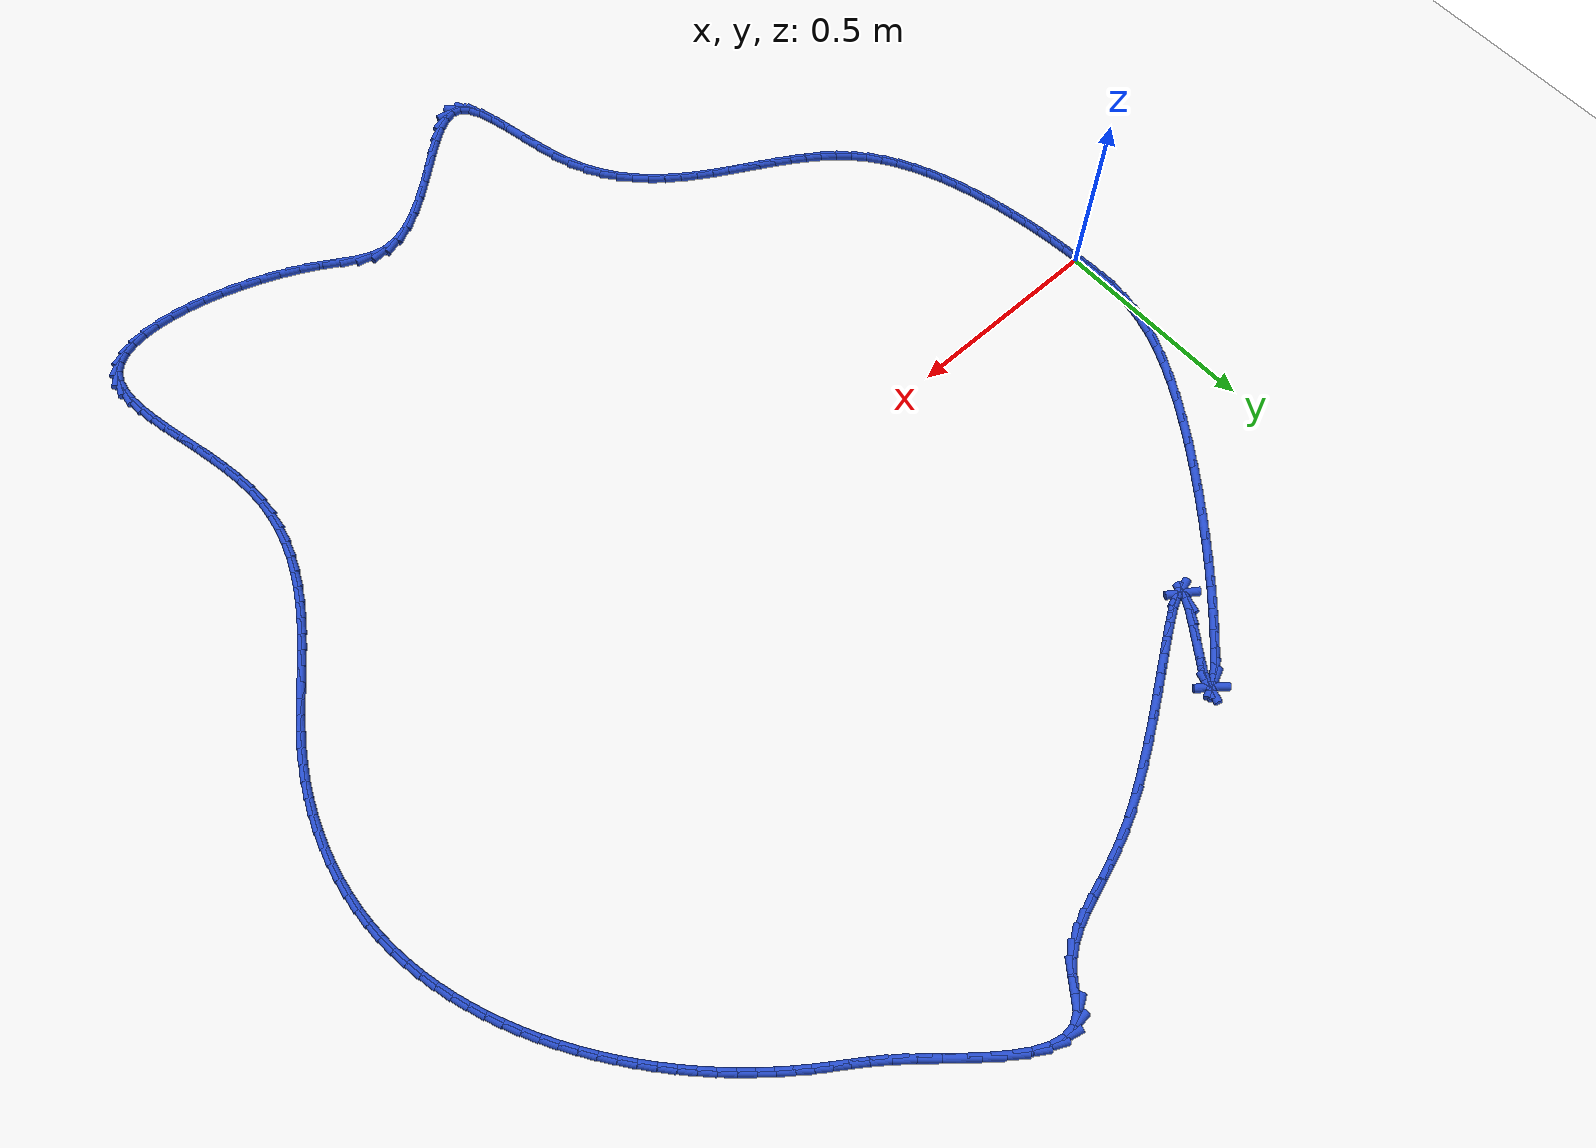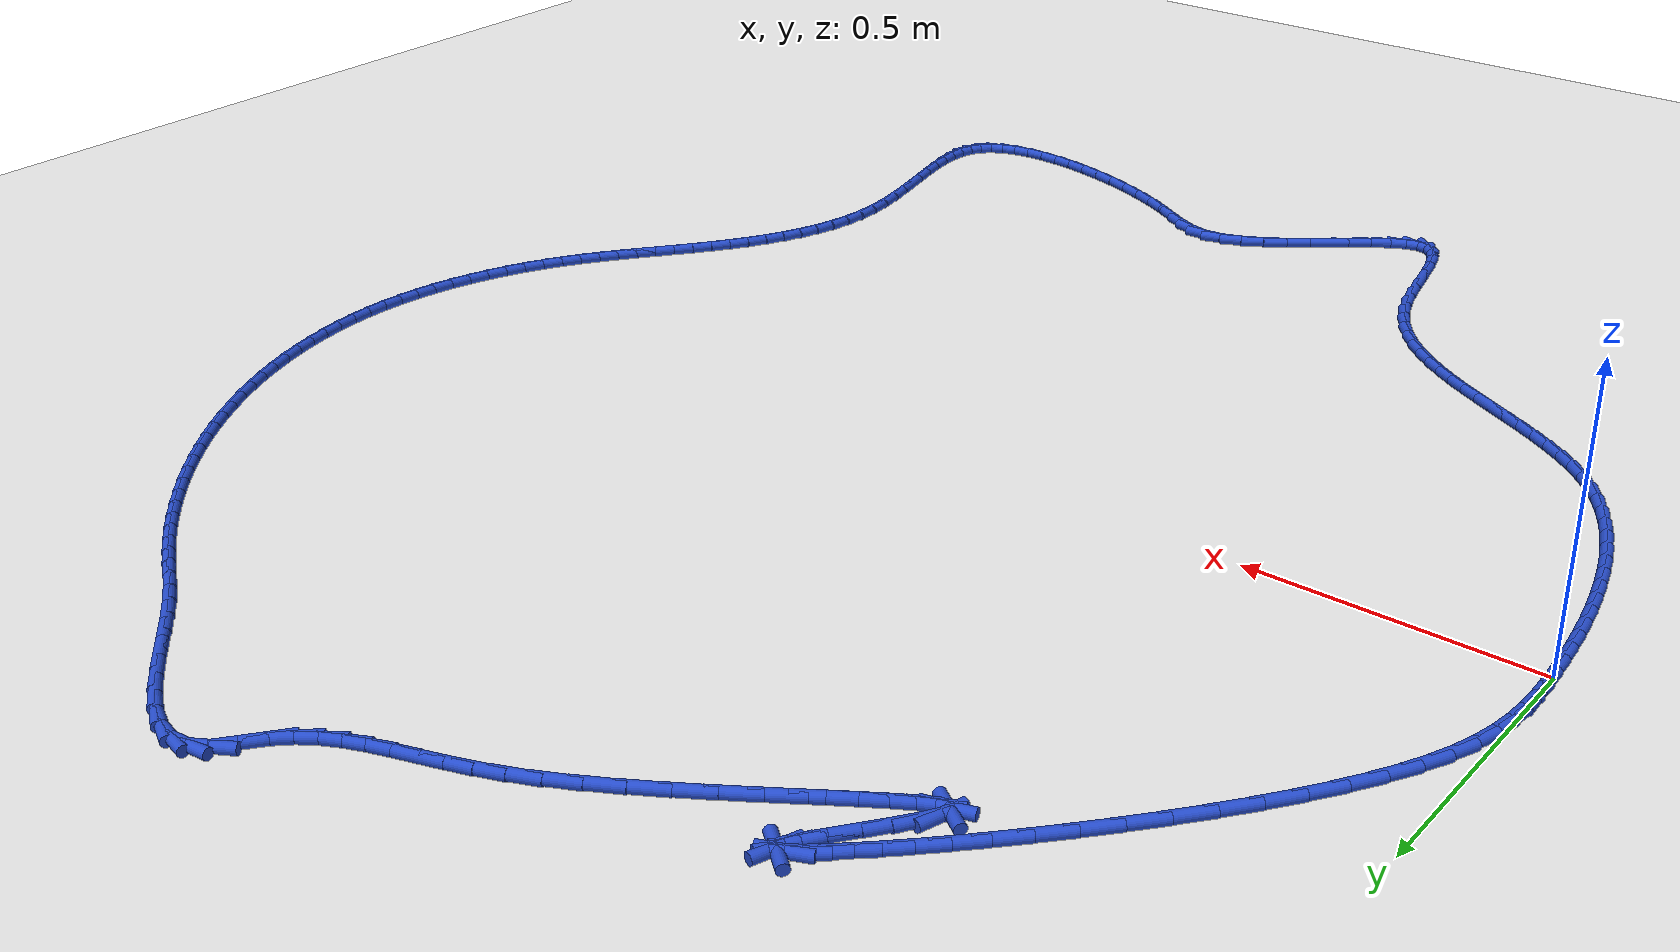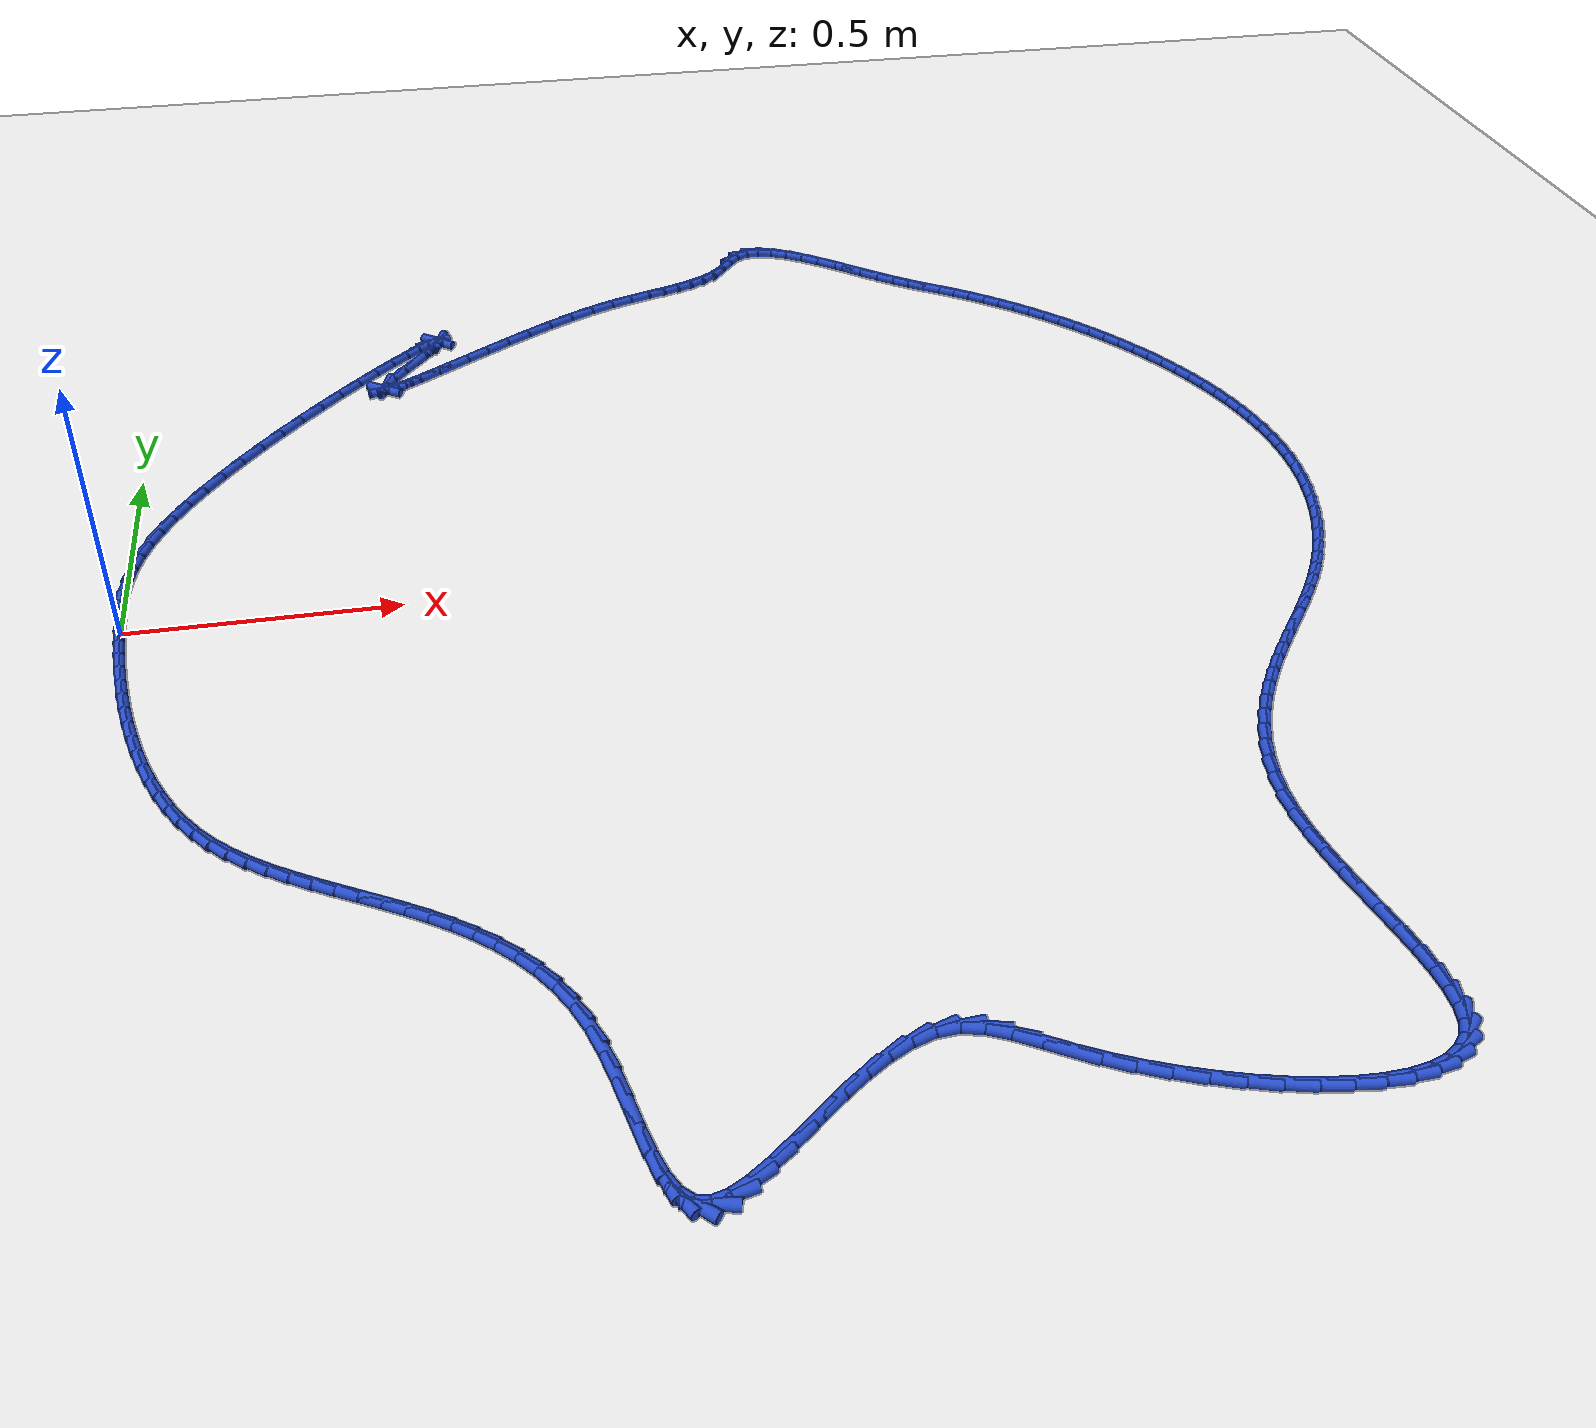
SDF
<sdf version="1.6">
 <world name="default">
  <light name="sun" type="directional">
   <pose>0 0 10 0 -0 0</pose>
   <diffuse>0.8 0.8 0.8 1</diffuse>
   <specular>0.2 0.2 0.2 1</specular>
   <attenuation>
    <range>1000</range>
    <constant>0.9</constant>
    <linear>0.01</linear>
    <quadratic>0.001</quadratic>
   </attenuation>
   <direction>-0.5 0.1 -0.9</direction>
  </light>
  <model name="ground_plane">
   <static>1</static>
   <link name="link">
    <collision name="collision">
     <geometry><plane><normal>0 0 1</normal><size>100 100</size></plane></geometry>
     <surface><friction><ode><mu>100</mu><mu2>50</mu2></ode></friction></surface>
    </collision>
    <visual name="visual">
     <cast_shadows>0</cast_shadows>
     <geometry><plane><normal>0 0 1</normal><size>100 100</size></plane></geometry>
     <material>
      <script><uri>file://media/materials/scripts/gazebo.material</uri><name>Gazebo/WhiteGlow</name></script>
     </material>
    </visual>
   </link>
  </model>
  <gravity>0 0 -9.8</gravity>
  <magnetic_field>6e-06 2.3e-05 -4.2e-05</magnetic_field>
  <atmosphere type="adiabatic"/>
  <physics name="default_physics" default="0" type="ode">
   <max_step_size>0.001</max_step_size>
   <real_time_factor>1</real_time_factor>
   <real_time_update_rate>1000</real_time_update_rate>
  </physics>
  <scene><ambient>0.4 0.4 0.4 1</ambient><background>0.7 0.7 0.7 1</background><shadows>1</shadows></scene>
  <spherical_coordinates>
   <surface_model>EARTH_WGS84</surface_model>
   <latitude_deg>0</latitude_deg>
   <longitude_deg>0</longitude_deg>
   <elevation>0</elevation>
   <heading_deg>0</heading_deg>
  </spherical_coordinates>
  <model name="line">
   <link name="link_0">
    <pose>-5.421010862427522e-18 -6.245004513516506e-17 0.01 0 1.57 -1.516971738887557</pose>
    <collision name="collision">
     <geometry><cylinder><radius>0.01</radius><length>0.08</length></cylinder></geometry>
    </collision>
    <visual name="visual">
     <material>
      <script><name>Gazebo/Blue</name><uri>file://media/materials/scripts/gazebo.material</uri></script>
     </material>
     <geometry><cylinder><radius>0.01</radius><length>0.08</length></cylinder></geometry>
    </visual>
   </link>
   <link name="link_1">
    <pose>-0.0019677262206567684 0.036522818023814574 0.01 0 1.57 -1.5498940656108167</pose>
    <collision name="collision">
     <geometry><cylinder><radius>0.01</radius><length>0.08</length></cylinder></geometry>
    </collision>
    <visual name="visual">
     <material>
      <script><name>Gazebo/Blue</name><uri>file://media/materials/scripts/gazebo.material</uri></script>
     </material>
     <geometry><cylinder><radius>0.01</radius><length>0.08</length></cylinder></geometry>
    </visual>
   </link>
   <link name="link_2">
    <pose>-0.0027258256793479484 0.072786313303385 0.01 0 1.57 1.542573850887566</pose>
    <collision name="collision">
     <geometry><cylinder><radius>0.01</radius><length>0.08</length></cylinder></geometry>
    </collision>
    <visual name="visual">
     <material>
      <script><name>Gazebo/Blue</name><uri>file://media/materials/scripts/gazebo.material</uri></script>
     </material>
     <geometry><cylinder><radius>0.01</radius><length>0.08</length></cylinder></geometry>
    </visual>
   </link>
   <link name="link_3">
    <pose>-0.0016979489906153566 0.10919714322356291 0.01 0 1.57 1.4793379034176113</pose>
    <collision name="collision">
     <geometry><cylinder><radius>0.01</radius><length>0.08</length></cylinder></geometry>
    </collision>
    <visual name="visual">
     <material>
      <script><name>Gazebo/Blue</name><uri>file://media/materials/scripts/gazebo.material</uri></script>
     </material>
     <geometry><cylinder><radius>0.01</radius><length>0.08</length></cylinder></geometry>
    </visual>
   </link>
   <link name="link_4">
    <pose>0.0016922532309991837 0.14616196516920005 0.01 0 1.57 1.4054433089721208</pose>
    <collision name="collision">
     <geometry><cylinder><radius>0.01</radius><length>0.08</length></cylinder></geometry>
    </collision>
    <visual name="visual">
     <material>
      <script><name>Gazebo/Blue</name><uri>file://media/materials/scripts/gazebo.material</uri></script>
     </material>
     <geometry><cylinder><radius>0.01</radius><length>0.08</length></cylinder></geometry>
    </visual>
   </link>
   <link name="link_5">
    <pose>0.008021130370953857 0.18408743652514828 0.01 0 1.57 1.3253217344991335</pose>
    <collision name="collision">
     <geometry><cylinder><radius>0.01</radius><length>0.08</length></cylinder></geometry>
    </collision>
    <visual name="visual">
     <material>
      <script><name>Gazebo/Blue</name><uri>file://media/materials/scripts/gazebo.material</uri></script>
     </material>
     <geometry><cylinder><radius>0.01</radius><length>0.08</length></cylinder></geometry>
    </visual>
   </link>
   <link name="link_6">
    <pose>0.017865031814706844 0.22338021467625926 0.01 0 1.57 1.243656388170542</pose>
    <collision name="collision">
     <geometry><cylinder><radius>0.01</radius><length>0.08</length></cylinder></geometry>
    </collision>
    <visual name="visual">
     <material>
      <script><name>Gazebo/Blue</name><uri>file://media/materials/scripts/gazebo.material</uri></script>
     </material>
     <geometry><cylinder><radius>0.01</radius><length>0.08</length></cylinder></geometry>
    </visual>
   </link>
   <link name="link_7">
    <pose>0.03180030694771633 0.2644469570073847 0.01 0 1.57 1.1646350907035172</pose>
    <collision name="collision">
     <geometry><cylinder><radius>0.01</radius><length>0.08</length></cylinder></geometry>
    </collision>
    <visual name="visual">
     <material>
      <script><name>Gazebo/Blue</name><uri>file://media/materials/scripts/gazebo.material</uri></script>
     </material>
     <geometry><cylinder><radius>0.01</radius><length>0.08</length></cylinder></geometry>
    </visual>
   </link>
   <link name="link_8">
    <pose>0.050398222578810534 0.307690395071881 0.01 0 1.57 1.0955145047660175</pose>
    <collision name="collision">
     <geometry><cylinder><radius>0.01</radius><length>0.08</length></cylinder></geometry>
    </collision>
    <visual name="visual">
     <material>
      <script><name>Gazebo/Blue</name><uri>file://media/materials/scripts/gazebo.material</uri></script>
     </material>
     <geometry><cylinder><radius>0.01</radius><length>0.08</length></cylinder></geometry>
    </visual>
   </link>
   <link name="link_9">
    <pose>0.07381498965637319 0.35319266725000886 0.01 0 1.57 1.041306595246719</pose>
    <collision name="collision">
     <geometry><cylinder><radius>0.01</radius><length>0.08</length></cylinder></geometry>
    </collision>
    <visual name="visual">
     <material>
      <script><name>Gazebo/Blue</name><uri>file://media/materials/scripts/gazebo.material</uri></script>
     </material>
     <geometry><cylinder><radius>0.01</radius><length>0.08</length></cylinder></geometry>
    </visual>
   </link>
   <link name="link_10">
    <pose>0.10149063260583117 0.40048272250391725 0.01 0 1.57 0.998125263919502</pose>
    <collision name="collision">
     <geometry><cylinder><radius>0.01</radius><length>0.08</length></cylinder></geometry>
    </collision>
    <visual name="visual">
     <material>
      <script><name>Gazebo/Blue</name><uri>file://media/materials/scripts/gazebo.material</uri></script>
     </material>
     <geometry><cylinder><radius>0.01</radius><length>0.08</length></cylinder></geometry>
    </visual>
   </link>
   <link name="link_11">
    <pose>0.1327941896283823 0.4490346793475182 0.01 0 1.57 0.9628135906939901</pose>
    <collision name="collision">
     <geometry><cylinder><radius>0.01</radius><length>0.08</length></cylinder></geometry>
    </collision>
    <visual name="visual">
     <material>
      <script><name>Gazebo/Blue</name><uri>file://media/materials/scripts/gazebo.material</uri></script>
     </material>
     <geometry><cylinder><radius>0.01</radius><length>0.08</length></cylinder></geometry>
    </visual>
   </link>
   <link name="link_12">
    <pose>0.16709469892522447 0.4983226562947236 0.01 0 1.57 0.9332314967239804</pose>
    <collision name="collision">
     <geometry><cylinder><radius>0.01</radius><length>0.08</length></cylinder></geometry>
    </collision>
    <visual name="visual">
     <material>
      <script><name>Gazebo/Blue</name><uri>file://media/materials/scripts/gazebo.material</uri></script>
     </material>
     <geometry><cylinder><radius>0.01</radius><length>0.08</length></cylinder></geometry>
    </visual>
   </link>
   <link name="link_13">
    <pose>0.20376119869755566 0.5478207718594456 0.01 0 1.57 0.9078736980603397</pose>
    <collision name="collision">
     <geometry><cylinder><radius>0.01</radius><length>0.08</length></cylinder></geometry>
    </collision>
    <visual name="visual">
     <material>
      <script><name>Gazebo/Blue</name><uri>file://media/materials/scripts/gazebo.material</uri></script>
     </material>
     <geometry><cylinder><radius>0.01</radius><length>0.08</length></cylinder></geometry>
    </visual>
   </link>
   <link name="link_14">
    <pose>0.24216272714657391 0.597003144555596 0.01 0 1.57 0.8856361692368085</pose>
    <collision name="collision">
     <geometry><cylinder><radius>0.01</radius><length>0.08</length></cylinder></geometry>
    </collision>
    <visual name="visual">
     <material>
      <script><name>Gazebo/Blue</name><uri>file://media/materials/scripts/gazebo.material</uri></script>
     </material>
     <geometry><cylinder><radius>0.01</radius><length>0.08</length></cylinder></geometry>
    </visual>
   </link>
   <link name="link_15">
    <pose>0.28166832247347695 0.6453438928970868 0.01 0 1.57 0.8656667961104185</pose>
    <collision name="collision">
     <geometry><cylinder><radius>0.01</radius><length>0.08</length></cylinder></geometry>
    </collision>
    <visual name="visual">
     <material>
      <script><name>Gazebo/Blue</name><uri>file://media/materials/scripts/gazebo.material</uri></script>
     </material>
     <geometry><cylinder><radius>0.01</radius><length>0.08</length></cylinder></geometry>
    </visual>
   </link>
   <link name="link_16">
    <pose>0.3216470228794627 0.6923171353978297 0.01 0 1.57 0.8472622095039724</pose>
    <collision name="collision">
     <geometry><cylinder><radius>0.01</radius><length>0.08</length></cylinder></geometry>
    </collision>
    <visual name="visual">
     <material>
      <script><name>Gazebo/Blue</name><uri>file://media/materials/scripts/gazebo.material</uri></script>
     </material>
     <geometry><cylinder><radius>0.01</radius><length>0.08</length></cylinder></geometry>
    </visual>
   </link>
   <link name="link_17">
    <pose>0.3614678665657291 0.7373969905717369 0.01 0 1.57 0.8297862383139776</pose>
    <collision name="collision">
     <geometry><cylinder><radius>0.01</radius><length>0.08</length></cylinder></geometry>
    </collision>
    <visual name="visual">
     <material>
      <script><name>Gazebo/Blue</name><uri>file://media/materials/scripts/gazebo.material</uri></script>
     </material>
     <geometry><cylinder><radius>0.01</radius><length>0.08</length></cylinder></geometry>
    </visual>
   </link>
   <link name="link_18">
    <pose>0.4004998917334741 0.7800575769327205 0.01 0 1.57 0.8125898857126308</pose>
    <collision name="collision">
     <geometry><cylinder><radius>0.01</radius><length>0.08</length></cylinder></geometry>
    </collision>
    <visual name="visual">
     <material>
      <script><name>Gazebo/Blue</name><uri>file://media/materials/scripts/gazebo.material</uri></script>
     </material>
     <geometry><cylinder><radius>0.01</radius><length>0.08</length></cylinder></geometry>
    </visual>
   </link>
   <link name="link_19">
    <pose>0.43811213658389586 0.8197730129946923 0.01 0 1.57 0.7949082578066576</pose>
    <collision name="collision">
     <geometry><cylinder><radius>0.01</radius><length>0.08</length></cylinder></geometry>
    </collision>
    <visual name="visual">
     <material>
      <script><name>Gazebo/Blue</name><uri>file://media/materials/scripts/gazebo.material</uri></script>
     </material>
     <geometry><cylinder><radius>0.01</radius><length>0.08</length></cylinder></geometry>
    </visual>
   </link>
   <link name="link_20">
    <pose>0.47367363931819195 0.8560174172715643 0.01 0 1.57 0.7756896687060839</pose>
    <collision name="collision">
     <geometry><cylinder><radius>0.01</radius><length>0.08</length></cylinder></geometry>
    </collision>
    <visual name="visual">
     <material>
      <script><name>Gazebo/Blue</name><uri>file://media/materials/scripts/gazebo.material</uri></script>
     </material>
     <geometry><cylinder><radius>0.01</radius><length>0.08</length></cylinder></geometry>
    </visual>
   </link>
   <link name="link_21">
    <pose>0.5065534381375605 0.8882649082772485 0.01 0 1.57 0.7532504360639813</pose>
    <collision name="collision">
     <geometry><cylinder><radius>0.01</radius><length>0.08</length></cylinder></geometry>
    </collision>
    <visual name="visual">
     <material>
      <script><name>Gazebo/Blue</name><uri>file://media/materials/scripts/gazebo.material</uri></script>
     </material>
     <geometry><cylinder><radius>0.01</radius><length>0.08</length></cylinder></geometry>
    </visual>
   </link>
   <link name="link_22">
    <pose>0.5361205712431993 0.9159896045256567 0.01 0 1.57 0.7244486027931144</pose>
    <collision name="collision">
     <geometry><cylinder><radius>0.01</radius><length>0.08</length></cylinder></geometry>
    </collision>
    <visual name="visual">
     <material>
      <script><name>Gazebo/Blue</name><uri>file://media/materials/scripts/gazebo.material</uri></script>
     </material>
     <geometry><cylinder><radius>0.01</radius><length>0.08</length></cylinder></geometry>
    </visual>
   </link>
   <link name="link_23">
    <pose>0.5617440768363061 0.9386656245307008 0.01 0 1.57 0.6822941702992007</pose>
    <collision name="collision">
     <geometry><cylinder><radius>0.01</radius><length>0.08</length></cylinder></geometry>
    </collision>
    <visual name="visual">
     <material>
      <script><name>Gazebo/Blue</name><uri>file://media/materials/scripts/gazebo.material</uri></script>
     </material>
     <geometry><cylinder><radius>0.01</radius><length>0.08</length></cylinder></geometry>
    </visual>
   </link>
   <link name="link_24">
    <pose>0.5827929931180793 0.9557670868062931 0.01 0 1.57 0.606931714351735</pose>
    <collision name="collision">
     <geometry><cylinder><radius>0.01</radius><length>0.08</length></cylinder></geometry>
    </collision>
    <visual name="visual">
     <material>
      <script><name>Gazebo/Blue</name><uri>file://media/materials/scripts/gazebo.material</uri></script>
     </material>
     <geometry><cylinder><radius>0.01</radius><length>0.08</length></cylinder></geometry>
    </visual>
   </link>
   <link name="link_25">
    <pose>0.5986363582897163 0.9667681098663448 0.01 0 1.57 0.4121339911330432</pose>
    <collision name="collision">
     <geometry><cylinder><radius>0.01</radius><length>0.08</length></cylinder></geometry>
    </collision>
    <visual name="visual">
     <material>
      <script><name>Gazebo/Blue</name><uri>file://media/materials/scripts/gazebo.material</uri></script>
     </material>
     <geometry><cylinder><radius>0.01</radius><length>0.08</length></cylinder></geometry>
    </visual>
   </link>
   <link name="link_26">
    <pose>0.6086432105524155 0.9711428122247691 0.01 0 1.57 -0.6653680736597327</pose>
    <collision name="collision">
     <geometry><cylinder><radius>0.01</radius><length>0.08</length></cylinder></geometry>
    </collision>
    <visual name="visual">
     <material>
      <script><name>Gazebo/Blue</name><uri>file://media/materials/scripts/gazebo.material</uri></script>
     </material>
     <geometry><cylinder><radius>0.01</radius><length>0.08</length></cylinder></geometry>
    </visual>
   </link>
   <link name="link_27">
    <pose>0.6121825881073746 0.9683653123954771 0.01 0 1.57 1.242701169890033</pose>
    <collision name="collision">
     <geometry><cylinder><radius>0.01</radius><length>0.08</length></cylinder></geometry>
    </collision>
    <visual name="visual">
     <material>
      <script><name>Gazebo/Blue</name><uri>file://media/materials/scripts/gazebo.material</uri></script>
     </material>
     <geometry><cylinder><radius>0.01</radius><length>0.08</length></cylinder></geometry>
    </visual>
   </link>
   <link name="link_28">
    <pose>0.6086235291557914 0.9579097288923809 0.01 0 1.57 1.0267308145427323</pose>
    <collision name="collision">
     <geometry><cylinder><radius>0.01</radius><length>0.08</length></cylinder></geometry>
    </collision>
    <visual name="visual">
     <material>
      <script><name>Gazebo/Blue</name><uri>file://media/materials/scripts/gazebo.material</uri></script>
     </material>
     <geometry><cylinder><radius>0.01</radius><length>0.08</length></cylinder></geometry>
    </visual>
   </link>
   <link name="link_29">
    <pose>0.597335071898864 0.9392501802293926 0.01 0 1.57 0.9500358720568822</pose>
    <collision name="collision">
     <geometry><cylinder><radius>0.01</radius><length>0.08</length></cylinder></geometry>
    </collision>
    <visual name="visual">
     <material>
      <script><name>Gazebo/Blue</name><uri>file://media/materials/scripts/gazebo.material</uri></script>
     </material>
     <geometry><cylinder><radius>0.01</radius><length>0.08</length></cylinder></geometry>
    </visual>
   </link>
   <link name="link_30">
    <pose>0.577900679022999 0.9120714030815712 0.01 0 1.57 0.9229881037805641</pose>
    <collision name="collision">
     <geometry><cylinder><radius>0.01</radius><length>0.08</length></cylinder></geometry>
    </collision>
    <visual name="visual">
     <material>
      <script><name>Gazebo/Blue</name><uri>file://media/materials/scripts/gazebo.material</uri></script>
     </material>
     <geometry><cylinder><radius>0.01</radius><length>0.08</length></cylinder></geometry>
    </visual>
   </link>
   <link name="link_31">
    <pose>0.5528014206703311 0.8789043051359231 0.01 0 1.57 0.9223799997988826</pose>
    <collision name="collision">
     <geometry><cylinder><radius>0.01</radius><length>0.08</length></cylinder></geometry>
    </collision>
    <visual name="visual">
     <material>
      <script><name>Gazebo/Blue</name><uri>file://media/materials/scripts/gazebo.material</uri></script>
     </material>
     <geometry><cylinder><radius>0.01</radius><length>0.08</length></cylinder></geometry>
    </visual>
   </link>
   <link name="link_32">
    <pose>0.5265999586464951 0.8443244346810134 0.01 0 1.57 0.9445234965934007</pose>
    <collision name="collision">
     <geometry><cylinder><radius>0.01</radius><length>0.08</length></cylinder></geometry>
    </collision>
    <visual name="visual">
     <material>
      <script><name>Gazebo/Blue</name><uri>file://media/materials/scripts/gazebo.material</uri></script>
     </material>
     <geometry><cylinder><radius>0.01</radius><length>0.08</length></cylinder></geometry>
    </visual>
   </link>
   <link name="link_33">
    <pose>0.5039045586338088 0.8129521343517196 0.01 0 1.57 1.0159028905434107</pose>
    <collision name="collision">
     <geometry><cylinder><radius>0.01</radius><length>0.08</length></cylinder></geometry>
    </collision>
    <visual name="visual">
     <material>
      <script><name>Gazebo/Blue</name><uri>file://media/materials/scripts/gazebo.material</uri></script>
     </material>
     <geometry><cylinder><radius>0.01</radius><length>0.08</length></cylinder></geometry>
    </visual>
   </link>
   <link name="link_34">
    <pose>0.4892876046066976 0.7893710163203097 0.01 0 1.57 1.2760694479814363</pose>
    <collision name="collision">
     <geometry><cylinder><radius>0.01</radius><length>0.08</length></cylinder></geometry>
    </collision>
    <visual name="visual">
     <material>
      <script><name>Gazebo/Blue</name><uri>file://media/materials/scripts/gazebo.material</uri></script>
     </material>
     <geometry><cylinder><radius>0.01</radius><length>0.08</length></cylinder></geometry>
    </visual>
   </link>
   <link name="link_35">
    <pose>0.48523841470276363 0.7760323535721672 0.01 0 1.57 -0.5916208756530282</pose>
    <collision name="collision">
     <geometry><cylinder><radius>0.01</radius><length>0.08</length></cylinder></geometry>
    </collision>
    <visual name="visual">
     <material>
      <script><name>Gazebo/Blue</name><uri>file://media/materials/scripts/gazebo.material</uri></script>
     </material>
     <geometry><cylinder><radius>0.01</radius><length>0.08</length></cylinder></geometry>
    </visual>
   </link>
   <link name="link_36">
    <pose>0.49105708342145665 0.7721227567766041 0.01 0 1.57 0.29238355709120445</pose>
    <collision name="collision">
     <geometry><cylinder><radius>0.01</radius><length>0.08</length></cylinder></geometry>
    </collision>
    <visual name="visual">
     <material>
      <script><name>Gazebo/Blue</name><uri>file://media/materials/scripts/gazebo.material</uri></script>
     </material>
     <geometry><cylinder><radius>0.01</radius><length>0.08</length></cylinder></geometry>
    </visual>
   </link>
   <link name="link_37">
    <pose>0.5057739319562572 0.7765526820130366 0.01 0 1.57 0.4761877554910015</pose>
    <collision name="collision">
     <geometry><cylinder><radius>0.01</radius><length>0.08</length></cylinder></geometry>
    </collision>
    <visual name="visual">
     <material>
      <script><name>Gazebo/Blue</name><uri>file://media/materials/scripts/gazebo.material</uri></script>
     </material>
     <geometry><cylinder><radius>0.01</radius><length>0.08</length></cylinder></geometry>
    </visual>
   </link>
   <link name="link_38">
    <pose>0.528419281500646 0.7882325853608815 0.01 0 1.57 0.5423504735451992</pose>
    <collision name="collision">
     <geometry><cylinder><radius>0.01</radius><length>0.08</length></cylinder></geometry>
    </collision>
    <visual name="visual">
     <material>
      <script><name>Gazebo/Blue</name><uri>file://media/materials/scripts/gazebo.material</uri></script>
     </material>
     <geometry><cylinder><radius>0.01</radius><length>0.08</length></cylinder></geometry>
    </visual>
   </link>
   <link name="link_39">
    <pose>0.5580234532481033 0.8060729228995551 0.01 0 1.57 0.5719298837502761</pose>
    <collision name="collision">
     <geometry><cylinder><radius>0.01</radius><length>0.08</length></cylinder></geometry>
    </collision>
    <visual name="visual">
     <material>
      <script><name>Gazebo/Blue</name><uri>file://media/materials/scripts/gazebo.material</uri></script>
     </material>
     <geometry><cylinder><radius>0.01</radius><length>0.08</length></cylinder></geometry>
    </visual>
   </link>
   <link name="link_40">
    <pose>0.5936167683921101 0.8289841507084734 0.01 0 1.57 0.5848832302612053</pose>
    <collision name="collision">
     <geometry><cylinder><radius>0.01</radius><length>0.08</length></cylinder></geometry>
    </collision>
    <visual name="visual">
     <material>
      <script><name>Gazebo/Blue</name><uri>file://media/materials/scripts/gazebo.material</uri></script>
     </material>
     <geometry><cylinder><radius>0.01</radius><length>0.08</length></cylinder></geometry>
    </visual>
   </link>
   <link name="link_41">
    <pose>0.634229548126147 0.8558767248670534 0.01 0 1.57 0.5881472576147512</pose>
    <collision name="collision">
     <geometry><cylinder><radius>0.01</radius><length>0.08</length></cylinder></geometry>
    </collision>
    <visual name="visual">
     <material>
      <script><name>Gazebo/Blue</name><uri>file://media/materials/scripts/gazebo.material</uri></script>
     </material>
     <geometry><cylinder><radius>0.01</radius><length>0.08</length></cylinder></geometry>
    </visual>
   </link>
   <link name="link_42">
    <pose>0.6788921136436937 0.8856611014547106 0.01 0 1.57 0.5844879127156619</pose>
    <collision name="collision">
     <geometry><cylinder><radius>0.01</radius><length>0.08</length></cylinder></geometry>
    </collision>
    <visual name="visual">
     <material>
      <script><name>Gazebo/Blue</name><uri>file://media/materials/scripts/gazebo.material</uri></script>
     </material>
     <geometry><cylinder><radius>0.01</radius><length>0.08</length></cylinder></geometry>
    </visual>
   </link>
   <link name="link_43">
    <pose>0.7266347861382322 0.9172477365508622 0.01 0 1.57 0.574890829373551</pose>
    <collision name="collision">
     <geometry><cylinder><radius>0.01</radius><length>0.08</length></cylinder></geometry>
    </collision>
    <visual name="visual">
     <material>
      <script><name>Gazebo/Blue</name><uri>file://media/materials/scripts/gazebo.material</uri></script>
     </material>
     <geometry><cylinder><radius>0.01</radius><length>0.08</length></cylinder></geometry>
    </visual>
   </link>
   <link name="link_44">
    <pose>0.7764878868032421 0.9495470862349243 0.01 0 1.57 0.5593233095142008</pose>
    <collision name="collision">
     <geometry><cylinder><radius>0.01</radius><length>0.08</length></cylinder></geometry>
    </collision>
    <visual name="visual">
     <material>
      <script><name>Gazebo/Blue</name><uri>file://media/materials/scripts/gazebo.material</uri></script>
     </material>
     <geometry><cylinder><radius>0.01</radius><length>0.08</length></cylinder></geometry>
    </visual>
   </link>
   <link name="link_45">
    <pose>0.8274817368322038 0.9814696065863133 0.01 0 1.57 0.5369228250322726</pose>
    <collision name="collision">
     <geometry><cylinder><radius>0.01</radius><length>0.08</length></cylinder></geometry>
    </collision>
    <visual name="visual">
     <material>
      <script><name>Gazebo/Blue</name><uri>file://media/materials/scripts/gazebo.material</uri></script>
     </material>
     <geometry><cylinder><radius>0.01</radius><length>0.08</length></cylinder></geometry>
    </visual>
   </link>
   <link name="link_46">
    <pose>0.8786466574185986 1.0119257536844453 0.01 0 1.57 0.5058679131148842</pose>
    <collision name="collision">
     <geometry><cylinder><radius>0.01</radius><length>0.08</length></cylinder></geometry>
    </collision>
    <visual name="visual">
     <material>
      <script><name>Gazebo/Blue</name><uri>file://media/materials/scripts/gazebo.material</uri></script>
     </material>
     <geometry><cylinder><radius>0.01</radius><length>0.08</length></cylinder></geometry>
    </visual>
   </link>
   <link name="link_47">
    <pose>0.9290129697559066 1.0398259836087371 0.01 0 1.57 0.4629190210279038</pose>
    <collision name="collision">
     <geometry><cylinder><radius>0.01</radius><length>0.08</length></cylinder></geometry>
    </collision>
    <visual name="visual">
     <material>
      <script><name>Gazebo/Blue</name><uri>file://media/materials/scripts/gazebo.material</uri></script>
     </material>
     <geometry><cylinder><radius>0.01</radius><length>0.08</length></cylinder></geometry>
    </visual>
   </link>
   <link name="link_48">
    <pose>0.9776109950376088 1.064080752438605 0.01 0 1.57 0.4070068377920131</pose>
    <collision name="collision">
     <geometry><cylinder><radius>0.01</radius><length>0.08</length></cylinder></geometry>
    </collision>
    <visual name="visual">
     <material>
      <script><name>Gazebo/Blue</name><uri>file://media/materials/scripts/gazebo.material</uri></script>
     </material>
     <geometry><cylinder><radius>0.01</radius><length>0.08</length></cylinder></geometry>
    </visual>
   </link>
   <link name="link_49">
    <pose>1.023609973890626 1.0839098650117842 0.01 0 1.57 0.35722260214612905</pose>
    <collision name="collision">
     <geometry><cylinder><radius>0.01</radius><length>0.08</length></cylinder></geometry>
    </collision>
    <visual name="visual">
     <material>
      <script><name>Gazebo/Blue</name><uri>file://media/materials/scripts/gazebo.material</uri></script>
     </material>
     <geometry><cylinder><radius>0.01</radius><length>0.08</length></cylinder></geometry>
    </visual>
   </link>
   <link name="link_50">
    <pose>1.066861637570058 1.1000529108582113 0.01 0 1.57 0.3248698915195105</pose>
    <collision name="collision">
     <geometry><cylinder><radius>0.01</radius><length>0.08</length></cylinder></geometry>
    </collision>
    <visual name="visual">
     <material>
      <script><name>Gazebo/Blue</name><uri>file://media/materials/scripts/gazebo.material</uri></script>
     </material>
     <geometry><cylinder><radius>0.01</radius><length>0.08</length></cylinder></geometry>
    </visual>
   </link>
   <link name="link_51">
    <pose>1.10742696149526 1.1137154288771396 0.01 0 1.57 0.3155936310310976</pose>
    <collision name="collision">
     <geometry><cylinder><radius>0.01</radius><length>0.08</length></cylinder></geometry>
    </collision>
    <visual name="visual">
     <material>
      <script><name>Gazebo/Blue</name><uri>file://media/materials/scripts/gazebo.material</uri></script>
     </material>
     <geometry><cylinder><radius>0.01</radius><length>0.08</length></cylinder></geometry>
    </visual>
   </link>
   <link name="link_52">
    <pose>1.1453669759045038 1.1261030800397562 0.01 0 1.57 0.33508584410469416</pose>
    <collision name="collision">
     <geometry><cylinder><radius>0.01</radius><length>0.08</length></cylinder></geometry>
    </collision>
    <visual name="visual">
     <material>
      <script><name>Gazebo/Blue</name><uri>file://media/materials/scripts/gazebo.material</uri></script>
     </material>
     <geometry><cylinder><radius>0.01</radius><length>0.08</length></cylinder></geometry>
    </visual>
   </link>
   <link name="link_53">
    <pose>1.1807427110360598 1.1384215253172485 0.01 0 1.57 0.3885028176982189</pose>
    <collision name="collision">
     <geometry><cylinder><radius>0.01</radius><length>0.08</length></cylinder></geometry>
    </collision>
    <visual name="visual">
     <material>
      <script><name>Gazebo/Blue</name><uri>file://media/materials/scripts/gazebo.material</uri></script>
     </material>
     <geometry><cylinder><radius>0.01</radius><length>0.08</length></cylinder></geometry>
    </visual>
   </link>
   <link name="link_54">
    <pose>1.2136151971281988 1.1518764256808025 0.01 0 1.57 0.4788277985845031</pose>
    <collision name="collision">
     <geometry><cylinder><radius>0.01</radius><length>0.08</length></cylinder></geometry>
    </collision>
    <visual name="visual">
     <material>
      <script><name>Gazebo/Blue</name><uri>file://media/materials/scripts/gazebo.material</uri></script>
     </material>
     <geometry><cylinder><radius>0.01</radius><length>0.08</length></cylinder></geometry>
    </visual>
   </link>
   <link name="link_55">
    <pose>1.2440454644191927 1.1676734421016062 0.01 0 1.57 0.6037638590888188</pose>
    <collision name="collision">
     <geometry><cylinder><radius>0.01</radius><length>0.08</length></cylinder></geometry>
    </collision>
    <visual name="visual">
     <material>
      <script><name>Gazebo/Blue</name><uri>file://media/materials/scripts/gazebo.material</uri></script>
     </material>
     <geometry><cylinder><radius>0.01</radius><length>0.08</length></cylinder></geometry>
    </visual>
   </link>
   <link name="link_56">
    <pose>1.272094543147313 1.1870182355508465 0.01 0 1.57 0.7526829251339359</pose>
    <collision name="collision">
     <geometry><cylinder><radius>0.01</radius><length>0.08</length></cylinder></geometry>
    </collision>
    <visual name="visual">
     <material>
      <script><name>Gazebo/Blue</name><uri>file://media/materials/scripts/gazebo.material</uri></script>
     </material>
     <geometry><cylinder><radius>0.01</radius><length>0.08</length></cylinder></geometry>
    </visual>
   </link>
   <link name="link_57">
    <pose>1.2978234635508303 1.2111164669997105 0.01 0 1.57 0.9059553250589817</pose>
    <collision name="collision">
     <geometry><cylinder><radius>0.01</radius><length>0.08</length></cylinder></geometry>
    </collision>
    <visual name="visual">
     <material>
      <script><name>Gazebo/Blue</name><uri>file://media/materials/scripts/gazebo.material</uri></script>
     </material>
     <geometry><cylinder><radius>0.01</radius><length>0.08</length></cylinder></geometry>
    </visual>
   </link>
   <link name="link_58">
    <pose>1.3213170246809662 1.2410869049250188 0.01 0 1.57 0.8987611843049171</pose>
    <collision name="collision">
     <geometry><cylinder><radius>0.01</radius><length>0.08</length></cylinder></geometry>
    </collision>
    <visual name="visual">
     <material>
      <script><name>Gazebo/Blue</name><uri>file://media/materials/scripts/gazebo.material</uri></script>
     </material>
     <geometry><cylinder><radius>0.01</radius><length>0.08</length></cylinder></geometry>
    </visual>
   </link>
   <link name="link_59">
    <pose>1.344722086734106 1.2705060652446905 0.01 0 1.57 0.538504190623126</pose>
    <collision name="collision">
     <geometry><cylinder><radius>0.01</radius><length>0.08</length></cylinder></geometry>
    </collision>
    <visual name="visual">
     <material>
      <script><name>Gazebo/Blue</name><uri>file://media/materials/scripts/gazebo.material</uri></script>
     </material>
     <geometry><cylinder><radius>0.01</radius><length>0.08</length></cylinder></geometry>
    </visual>
   </link>
   <link name="link_60">
    <pose>1.371756844949033 1.2866565802121317 0.01 0 1.57 0.1029266934992605</pose>
    <collision name="collision">
     <geometry><cylinder><radius>0.01</radius><length>0.08</length></cylinder></geometry>
    </collision>
    <visual name="visual">
     <material>
      <script><name>Gazebo/Blue</name><uri>file://media/materials/scripts/gazebo.material</uri></script>
     </material>
     <geometry><cylinder><radius>0.01</radius><length>0.08</length></cylinder></geometry>
    </visual>
   </link>
   <link name="link_61">
    <pose>1.4022825156770342 1.2898096288036562 0.01 0 1.57 -0.23081224614955703</pose>
    <collision name="collision">
     <geometry><cylinder><radius>0.01</radius><length>0.08</length></cylinder></geometry>
    </collision>
    <visual name="visual">
     <material>
      <script><name>Gazebo/Blue</name><uri>file://media/materials/scripts/gazebo.material</uri></script>
     </material>
     <geometry><cylinder><radius>0.01</radius><length>0.08</length></cylinder></geometry>
    </visual>
   </link>
   <link name="link_62">
    <pose>1.4356498783897376 1.2819682885050008 0.01 0 1.57 -0.44211050993414597</pose>
    <collision name="collision">
     <geometry><cylinder><radius>0.01</radius><length>0.08</length></cylinder></geometry>
    </collision>
    <visual name="visual">
     <material>
      <script><name>Gazebo/Blue</name><uri>file://media/materials/scripts/gazebo.material</uri></script>
     </material>
     <geometry><cylinder><radius>0.01</radius><length>0.08</length></cylinder></geometry>
    </visual>
   </link>
   <link name="link_63">
    <pose>1.4712097125587704 1.2651356368019018 0.01 0 1.57 -0.5707442001541588</pose>
    <collision name="collision">
     <geometry><cylinder><radius>0.01</radius><length>0.08</length></cylinder></geometry>
    </collision>
    <visual name="visual">
     <material>
      <script><name>Gazebo/Blue</name><uri>file://media/materials/scripts/gazebo.material</uri></script>
     </material>
     <geometry><cylinder><radius>0.01</radius><length>0.08</length></cylinder></geometry>
    </visual>
   </link>
   <link name="link_64">
    <pose>1.508312797655761 1.2413147511800955 0.01 0 1.57 -0.6486721518860892</pose>
    <collision name="collision">
     <geometry><cylinder><radius>0.01</radius><length>0.08</length></cylinder></geometry>
    </collision>
    <visual name="visual">
     <material>
      <script><name>Gazebo/Blue</name><uri>file://media/materials/scripts/gazebo.material</uri></script>
     </material>
     <geometry><cylinder><radius>0.01</radius><length>0.08</length></cylinder></geometry>
    </visual>
   </link>
   <link name="link_65">
    <pose>1.5463099131523372 1.212508709125319 0.01 0 1.57 -0.6935000931587936</pose>
    <collision name="collision">
     <geometry><cylinder><radius>0.01</radius><length>0.08</length></cylinder></geometry>
    </collision>
    <visual name="visual">
     <material>
      <script><name>Gazebo/Blue</name><uri>file://media/materials/scripts/gazebo.material</uri></script>
     </material>
     <geometry><cylinder><radius>0.01</radius><length>0.08</length></cylinder></geometry>
    </visual>
   </link>
   <link name="link_66">
    <pose>1.5845518385201265 1.1807205881233078 0.01 0 1.57 -0.7137073662212106</pose>
    <collision name="collision">
     <geometry><cylinder><radius>0.01</radius><length>0.08</length></cylinder></geometry>
    </collision>
    <visual name="visual">
     <material>
      <script><name>Gazebo/Blue</name><uri>file://media/materials/scripts/gazebo.material</uri></script>
     </material>
     <geometry><cylinder><radius>0.01</radius><length>0.08</length></cylinder></geometry>
    </visual>
   </link>
   <link name="link_67">
    <pose>1.6223893532307565 1.147953465659799 0.01 0 1.57 -0.7119704701663202</pose>
    <collision name="collision">
     <geometry><cylinder><radius>0.01</radius><length>0.08</length></cylinder></geometry>
    </collision>
    <visual name="visual">
     <material>
      <script><name>Gazebo/Blue</name><uri>file://media/materials/scripts/gazebo.material</uri></script>
     </material>
     <geometry><cylinder><radius>0.01</radius><length>0.08</length></cylinder></geometry>
    </visual>
   </link>
   <link name="link_68">
    <pose>1.6591732367558554 1.116210419220529 0.01 0 1.57 -0.6860928679042951</pose>
    <collision name="collision">
     <geometry><cylinder><radius>0.01</radius><length>0.08</length></cylinder></geometry>
    </collision>
    <visual name="visual">
     <material>
      <script><name>Gazebo/Blue</name><uri>file://media/materials/scripts/gazebo.material</uri></script>
     </material>
     <geometry><cylinder><radius>0.01</radius><length>0.08</length></cylinder></geometry>
    </visual>
   </link>
   <link name="link_69">
    <pose>1.6942580016570266 1.0874834138759824 0.01 0 1.57 -0.6434156469643703</pose>
    <collision name="collision">
     <geometry><cylinder><radius>0.01</radius><length>0.08</length></cylinder></geometry>
    </collision>
    <visual name="visual">
     <material>
      <script><name>Gazebo/Blue</name><uri>file://media/materials/scripts/gazebo.material</uri></script>
     </material>
     <geometry><cylinder><radius>0.01</radius><length>0.08</length></cylinder></geometry>
    </visual>
   </link>
   <link name="link_70">
    <pose>1.72737166648711 1.0626525867737122 0.01 0 1.57 -0.6109095546878873</pose>
    <collision name="collision">
     <geometry><cylinder><radius>0.01</radius><length>0.08</length></cylinder></geometry>
    </collision>
    <visual name="visual">
     <material>
      <script><name>Gazebo/Blue</name><uri>file://media/materials/scripts/gazebo.material</uri></script>
     </material>
     <geometry><cylinder><radius>0.01</radius><length>0.08</length></cylinder></geometry>
    </visual>
   </link>
   <link name="link_71">
    <pose>1.7589289924393543 1.0405538250053556 0.01 0 1.57 -0.5975692915439907</pose>
    <collision name="collision">
     <geometry><cylinder><radius>0.01</radius><length>0.08</length></cylinder></geometry>
    </collision>
    <visual name="visual">
     <material>
      <script><name>Gazebo/Blue</name><uri>file://media/materials/scripts/gazebo.material</uri></script>
     </material>
     <geometry><cylinder><radius>0.01</radius><length>0.08</length></cylinder></geometry>
    </visual>
   </link>
   <link name="link_72">
    <pose>1.7894185023409064 1.0198034469109531 0.01 0 1.57 -0.6073176363308823</pose>
    <collision name="collision">
     <geometry><cylinder><radius>0.01</radius><length>0.08</length></cylinder></geometry>
    </collision>
    <visual name="visual">
     <material>
      <script><name>Gazebo/Blue</name><uri>file://media/materials/scripts/gazebo.material</uri></script>
     </material>
     <geometry><cylinder><radius>0.01</radius><length>0.08</length></cylinder></geometry>
    </visual>
   </link>
   <link name="link_73">
    <pose>1.8193286851291117 0.9990178541445405 0.01 0 1.57 -0.6356355026045349</pose>
    <collision name="collision">
     <geometry><cylinder><radius>0.01</radius><length>0.08</length></cylinder></geometry>
    </collision>
    <visual name="visual">
     <material>
      <script><name>Gazebo/Blue</name><uri>file://media/materials/scripts/gazebo.material</uri></script>
     </material>
     <geometry><cylinder><radius>0.01</radius><length>0.08</length></cylinder></geometry>
    </visual>
   </link>
   <link name="link_74">
    <pose>1.8490293293869633 0.9771052588897906 0.01 0 1.57 -0.6665084572637888</pose>
    <collision name="collision">
     <geometry><cylinder><radius>0.01</radius><length>0.08</length></cylinder></geometry>
    </collision>
    <visual name="visual">
     <material>
      <script><name>Gazebo/Blue</name><uri>file://media/materials/scripts/gazebo.material</uri></script>
     </material>
     <geometry><cylinder><radius>0.01</radius><length>0.08</length></cylinder></geometry>
    </visual>
   </link>
   <link name="link_75">
    <pose>1.8785054861832955 0.9539197041864924 0.01 0 1.57 -0.697042996206371</pose>
    <collision name="collision">
     <geometry><cylinder><radius>0.01</radius><length>0.08</length></cylinder></geometry>
    </collision>
    <visual name="visual">
     <material>
      <script><name>Gazebo/Blue</name><uri>file://media/materials/scripts/gazebo.material</uri></script>
     </material>
     <geometry><cylinder><radius>0.01</radius><length>0.08</length></cylinder></geometry>
    </visual>
   </link>
   <link name="link_76">
    <pose>1.9076643957813002 0.9295065215716769 0.01 0 1.57 -0.7274364860579178</pose>
    <collision name="collision">
     <geometry><cylinder><radius>0.01</radius><length>0.08</length></cylinder></geometry>
    </collision>
    <visual name="visual">
     <material>
      <script><name>Gazebo/Blue</name><uri>file://media/materials/scripts/gazebo.material</uri></script>
     </material>
     <geometry><cylinder><radius>0.01</radius><length>0.08</length></cylinder></geometry>
    </visual>
   </link>
   <link name="link_77">
    <pose>1.9364132984441667 0.9039110425823745 0.01 0 1.57 -0.757872718635888</pose>
    <collision name="collision">
     <geometry><cylinder><radius>0.01</radius><length>0.08</length></cylinder></geometry>
    </collision>
    <visual name="visual">
     <material>
      <script><name>Gazebo/Blue</name><uri>file://media/materials/scripts/gazebo.material</uri></script>
     </material>
     <geometry><cylinder><radius>0.01</radius><length>0.08</length></cylinder></geometry>
    </visual>
   </link>
   <link name="link_78">
    <pose>1.9646594344350876 0.8771785987556159 0.01 0 1.57 -0.7885251207527355</pose>
    <collision name="collision">
     <geometry><cylinder><radius>0.01</radius><length>0.08</length></cylinder></geometry>
    </collision>
    <visual name="visual">
     <material>
      <script><name>Gazebo/Blue</name><uri>file://media/materials/scripts/gazebo.material</uri></script>
     </material>
     <geometry><cylinder><radius>0.01</radius><length>0.08</length></cylinder></geometry>
    </visual>
   </link>
   <link name="link_79">
    <pose>1.9923100440172534 0.8493545216284311 0.01 0 1.57 -0.8195593823646083</pose>
    <collision name="collision">
     <geometry><cylinder><radius>0.01</radius><length>0.08</length></cylinder></geometry>
    </collision>
    <visual name="visual">
     <material>
      <script><name>Gazebo/Blue</name><uri>file://media/materials/scripts/gazebo.material</uri></script>
     </material>
     <geometry><cylinder><radius>0.01</radius><length>0.08</length></cylinder></geometry>
    </visual>
   </link>
   <link name="link_80">
    <pose>2.019272367453855 0.8204841427378515 0.01 0 1.57 -0.8511355751033645</pose>
    <collision name="collision">
     <geometry><cylinder><radius>0.01</radius><length>0.08</length></cylinder></geometry>
    </collision>
    <visual name="visual">
     <material>
      <script><name>Gazebo/Blue</name><uri>file://media/materials/scripts/gazebo.material</uri></script>
     </material>
     <geometry><cylinder><radius>0.01</radius><length>0.08</length></cylinder></geometry>
    </visual>
   </link>
   <link name="link_81">
    <pose>2.0454536450080836 0.7906127936209075 0.01 0 1.57 -0.8834098047155189</pose>
    <collision name="collision">
     <geometry><cylinder><radius>0.01</radius><length>0.08</length></cylinder></geometry>
    </collision>
    <visual name="visual">
     <material>
      <script><name>Gazebo/Blue</name><uri>file://media/materials/scripts/gazebo.material</uri></script>
     </material>
     <geometry><cylinder><radius>0.01</radius><length>0.08</length></cylinder></geometry>
    </visual>
   </link>
   <link name="link_82">
    <pose>2.070761116943131 0.759785805814629 0.01 0 1.57 -0.9165354142175496</pose>
    <collision name="collision">
     <geometry><cylinder><radius>0.01</radius><length>0.08</length></cylinder></geometry>
    </collision>
    <visual name="visual">
     <material>
      <script><name>Gazebo/Blue</name><uri>file://media/materials/scripts/gazebo.material</uri></script>
     </material>
     <geometry><cylinder><radius>0.01</radius><length>0.08</length></cylinder></geometry>
    </visual>
   </link>
   <link name="link_83">
    <pose>2.095102023522187 0.7280485108560476 0.01 0 1.57 -0.9506485974878088</pose>
    <collision name="collision">
     <geometry><cylinder><radius>0.01</radius><length>0.08</length></cylinder></geometry>
    </collision>
    <visual name="visual">
     <material>
      <script><name>Gazebo/Blue</name><uri>file://media/materials/scripts/gazebo.material</uri></script>
     </material>
     <geometry><cylinder><radius>0.01</radius><length>0.08</length></cylinder></geometry>
    </visual>
   </link>
   <link name="link_84">
    <pose>2.118384052148855 0.6954466572381055 0.01 0 1.57 -0.9856612183004019</pose>
    <collision name="collision">
     <geometry><cylinder><radius>0.01</radius><length>0.08</length></cylinder></geometry>
    </collision>
    <visual name="visual">
     <material>
      <script><name>Gazebo/Blue</name><uri>file://media/materials/scripts/gazebo.material</uri></script>
     </material>
     <geometry><cylinder><radius>0.01</radius><length>0.08</length></cylinder></geometry>
    </visual>
   </link>
   <link name="link_85">
    <pose>2.140521962693448 0.6620325884890712 0.01 0 1.57 -1.0215367578809775</pose>
    <collision name="collision">
     <geometry><cylinder><radius>0.01</radius><length>0.08</length></cylinder></geometry>
    </collision>
    <visual name="visual">
     <material>
      <script><name>Gazebo/Blue</name><uri>file://media/materials/scripts/gazebo.material</uri></script>
     </material>
     <geometry><cylinder><radius>0.01</radius><length>0.08</length></cylinder></geometry>
    </visual>
   </link>
   <link name="link_86">
    <pose>2.161436161618046 0.6278639135521948 0.01 0 1.57 -1.0584244458451224</pose>
    <collision name="collision">
     <geometry><cylinder><radius>0.01</radius><length>0.08</length></cylinder></geometry>
    </collision>
    <visual name="visual">
     <material>
      <script><name>Gazebo/Blue</name><uri>file://media/materials/scripts/gazebo.material</uri></script>
     </material>
     <geometry><cylinder><radius>0.01</radius><length>0.08</length></cylinder></geometry>
    </visual>
   </link>
   <link name="link_87">
    <pose>2.1810472128104976 0.5929983881693672 0.01 0 1.57 -1.0964774613590542</pose>
    <collision name="collision">
     <geometry><cylinder><radius>0.01</radius><length>0.08</length></cylinder></geometry>
    </collision>
    <visual name="visual">
     <material>
      <script><name>Gazebo/Blue</name><uri>file://media/materials/scripts/gazebo.material</uri></script>
     </material>
     <geometry><cylinder><radius>0.01</radius><length>0.08</length></cylinder></geometry>
    </visual>
   </link>
   <link name="link_88">
    <pose>2.1992756801586504 0.5574937680824794 0.01 0 1.57 -1.1358468316778234</pose>
    <collision name="collision">
     <geometry><cylinder><radius>0.01</radius><length>0.08</length></cylinder></geometry>
    </collision>
    <visual name="visual">
     <material>
      <script><name>Gazebo/Blue</name><uri>file://media/materials/scripts/gazebo.material</uri></script>
     </material>
     <geometry><cylinder><radius>0.01</radius><length>0.08</length></cylinder></geometry>
    </visual>
   </link>
   <link name="link_89">
    <pose>2.2160421275503537 0.5214078090334238 0.01 0 1.57 -1.1766800010157241</pose>
    <collision name="collision">
     <geometry><cylinder><radius>0.01</radius><length>0.08</length></cylinder></geometry>
    </collision>
    <visual name="visual">
     <material>
      <script><name>Gazebo/Blue</name><uri>file://media/materials/scripts/gazebo.material</uri></script>
     </material>
     <geometry><cylinder><radius>0.01</radius><length>0.08</length></cylinder></geometry>
    </visual>
   </link>
   <link name="link_90">
    <pose>2.2312671188734567 0.48479826676409077 0.01 0 1.57 -1.2191186255877215</pose>
    <collision name="collision">
     <geometry><cylinder><radius>0.01</radius><length>0.08</length></cylinder></geometry>
    </collision>
    <visual name="visual">
     <material>
      <script><name>Gazebo/Blue</name><uri>file://media/materials/scripts/gazebo.material</uri></script>
     </material>
     <geometry><cylinder><radius>0.01</radius><length>0.08</length></cylinder></geometry>
    </visual>
   </link>
   <link name="link_91">
    <pose>2.244871218015808 0.44772289701637225 0.01 0 1.57 -1.2632954759078336</pose>
    <collision name="collision">
     <geometry><cylinder><radius>0.01</radius><length>0.08</length></cylinder></geometry>
    </collision>
    <visual name="visual">
     <material>
      <script><name>Gazebo/Blue</name><uri>file://media/materials/scripts/gazebo.material</uri></script>
     </material>
     <geometry><cylinder><radius>0.01</radius><length>0.08</length></cylinder></geometry>
    </visual>
   </link>
   <link name="link_92">
    <pose>2.256774988865257 0.41023945553215907 0.01 0 1.57 -1.3093303420247384</pose>
    <collision name="collision">
     <geometry><cylinder><radius>0.01</radius><length>0.08</length></cylinder></geometry>
    </collision>
    <visual name="visual">
     <material>
      <script><name>Gazebo/Blue</name><uri>file://media/materials/scripts/gazebo.material</uri></script>
     </material>
     <geometry><cylinder><radius>0.01</radius><length>0.08</length></cylinder></geometry>
    </visual>
   </link>
   <link name="link_93">
    <pose>2.2668989953096497 0.37240569805334317 0.01 0 1.57 -1.3573248775842262</pose>
    <collision name="collision">
     <geometry><cylinder><radius>0.01</radius><length>0.08</length></cylinder></geometry>
    </collision>
    <visual name="visual">
     <material>
      <script><name>Gazebo/Blue</name><uri>file://media/materials/scripts/gazebo.material</uri></script>
     </material>
     <geometry><cylinder><radius>0.01</radius><length>0.08</length></cylinder></geometry>
    </visual>
   </link>
   <link name="link_94">
    <pose>2.2751638012368374 0.33427938032181564 0.01 0 1.57 -1.4073563943673635</pose>
    <collision name="collision">
     <geometry><cylinder><radius>0.01</radius><length>0.08</length></cylinder></geometry>
    </collision>
    <visual name="visual">
     <material>
      <script><name>Gazebo/Blue</name><uri>file://media/materials/scripts/gazebo.material</uri></script>
     </material>
     <geometry><cylinder><radius>0.01</radius><length>0.08</length></cylinder></geometry>
    </visual>
   </link>
   <link name="link_95">
    <pose>2.281489970534668 0.29591825807946753 0.01 0 1.57 -1.4594707392036435</pose>
    <collision name="collision">
     <geometry><cylinder><radius>0.01</radius><length>0.08</length></cylinder></geometry>
    </collision>
    <visual name="visual">
     <material>
      <script><name>Gazebo/Blue</name><uri>file://media/materials/scripts/gazebo.material</uri></script>
     </material>
     <geometry><cylinder><radius>0.01</radius><length>0.08</length></cylinder></geometry>
    </visual>
   </link>
   <link name="link_96">
    <pose>2.28579806709099 0.25738008706819077 0.01 0 1.57 -1.513674554122117</pose>
    <collision name="collision">
     <geometry><cylinder><radius>0.01</radius><length>0.08</length></cylinder></geometry>
    </collision>
    <visual name="visual">
     <material>
      <script><name>Gazebo/Blue</name><uri>file://media/materials/scripts/gazebo.material</uri></script>
     </material>
     <geometry><cylinder><radius>0.01</radius><length>0.08</length></cylinder></geometry>
    </visual>
   </link>
   <link name="link_97">
    <pose>2.2880086547936527 0.21872262302987655 0.01 0 1.57 -1.5699274322667804</pose>
    <collision name="collision">
     <geometry><cylinder><radius>0.01</radius><length>0.08</length></cylinder></geometry>
    </collision>
    <visual name="visual">
     <material>
      <script><name>Gazebo/Blue</name><uri>file://media/materials/scripts/gazebo.material</uri></script>
     </material>
     <geometry><cylinder><radius>0.01</radius><length>0.08</length></cylinder></geometry>
    </visual>
   </link>
   <link name="link_98">
    <pose>2.2880422975305033 0.18000362170641565 0.01 0 1.57 1.513608441366449</pose>
    <collision name="collision">
     <geometry><cylinder><radius>0.01</radius><length>0.08</length></cylinder></geometry>
    </collision>
    <visual name="visual">
     <material>
      <script><name>Gazebo/Blue</name><uri>file://media/materials/scripts/gazebo.material</uri></script>
     </material>
     <geometry><cylinder><radius>0.01</radius><length>0.08</length></cylinder></geometry>
    </visual>
   </link>
   <link name="link_99">
    <pose>2.285825519514902 0.141282818370826 0.01 0 1.57 1.4560558930298946</pose>
    <collision name="collision">
     <geometry><cylinder><radius>0.01</radius><length>0.08</length></cylinder></geometry>
    </collision>
    <visual name="visual">
     <material>
      <script><name>Gazebo/Blue</name><uri>file://media/materials/scripts/gazebo.material</uri></script>
     </material>
     <geometry><cylinder><radius>0.01</radius><length>0.08</length></cylinder></geometry>
    </visual>
   </link>
   <link name="link_100">
    <pose>2.281373133192202 0.10264927040327847 0.01 0 1.57 1.400592252242638</pose>
    <collision name="collision">
     <geometry><cylinder><radius>0.01</radius><length>0.08</length></cylinder></geometry>
    </collision>
    <visual name="visual">
     <material>
      <script><name>Gazebo/Blue</name><uri>file://media/materials/scripts/gazebo.material</uri></script>
     </material>
     <geometry><cylinder><radius>0.01</radius><length>0.08</length></cylinder></geometry>
    </visual>
   </link>
   <link name="link_101">
    <pose>2.2747674601529386 0.06421445618325564 0.01 0 1.57 1.3470609814321004</pose>
    <collision name="collision">
     <geometry><cylinder><radius>0.01</radius><length>0.08</length></cylinder></geometry>
    </collision>
    <visual name="visual">
     <material>
      <script><name>Gazebo/Blue</name><uri>file://media/materials/scripts/gazebo.material</uri></script>
     </material>
     <geometry><cylinder><radius>0.01</radius><length>0.08</length></cylinder></geometry>
    </visual>
   </link>
   <link name="link_102">
    <pose>2.2660925324606254 0.02609042216903168 0.01 0 1.57 1.295236085773746</pose>
    <collision name="collision">
     <geometry><cylinder><radius>0.01</radius><length>0.08</length></cylinder></geometry>
    </collision>
    <visual name="visual">
     <material>
      <script><name>Gazebo/Blue</name><uri>file://media/materials/scripts/gazebo.material</uri></script>
     </material>
     <geometry><cylinder><radius>0.01</radius><length>0.08</length></cylinder></geometry>
    </visual>
   </link>
   <link name="link_103">
    <pose>2.2554323821787774 -0.011610785181120464 0.01 0 1.57 1.2448729225056592</pose>
    <collision name="collision">
     <geometry><cylinder><radius>0.01</radius><length>0.08</length></cylinder></geometry>
    </collision>
    <visual name="visual">
     <material>
      <script><name>Gazebo/Blue</name><uri>file://media/materials/scripts/gazebo.material</uri></script>
     </material>
     <geometry><cylinder><radius>0.01</radius><length>0.08</length></cylinder></geometry>
    </visual>
   </link>
   <link name="link_104">
    <pose>2.24287104137091 -0.04877711940892762 0.01 0 1.57 1.1957136526302299</pose>
    <collision name="collision">
     <geometry><cylinder><radius>0.01</radius><length>0.08</length></cylinder></geometry>
    </collision>
    <visual name="visual">
     <material>
      <script><name>Gazebo/Blue</name><uri>file://media/materials/scripts/gazebo.material</uri></script>
     </material>
     <geometry><cylinder><radius>0.01</radius><length>0.08</length></cylinder></geometry>
    </visual>
   </link>
   <link name="link_105">
    <pose>2.228492542100537 -0.08529653405611641 0.01 0 1.57 1.1474907966827188</pose>
    <collision name="collision">
     <geometry><cylinder><radius>0.01</radius><length>0.08</length></cylinder></geometry>
    </collision>
    <visual name="visual">
     <material>
      <script><name>Gazebo/Blue</name><uri>file://media/materials/scripts/gazebo.material</uri></script>
     </material>
     <geometry><cylinder><radius>0.01</radius><length>0.08</length></cylinder></geometry>
    </visual>
   </link>
   <link name="link_106">
    <pose>2.2123809164311727 -0.12105698266441442 0.01 0 1.57 1.0999292082882837</pose>
    <collision name="collision">
     <geometry><cylinder><radius>0.01</radius><length>0.08</length></cylinder></geometry>
    </collision>
    <visual name="visual">
     <material>
      <script><name>Gazebo/Blue</name><uri>file://media/materials/scripts/gazebo.material</uri></script>
     </material>
     <geometry><cylinder><radius>0.01</radius><length>0.08</length></cylinder></geometry>
    </visual>
   </link>
   <link name="link_107">
    <pose>2.1946201964263325 -0.15594641877554666 0.01 0 1.57 1.0527467801412542</pose>
    <collision name="collision">
     <geometry><cylinder><radius>0.01</radius><length>0.08</length></cylinder></geometry>
    </collision>
    <visual name="visual">
     <material>
      <script><name>Gazebo/Blue</name><uri>file://media/materials/scripts/gazebo.material</uri></script>
     </material>
     <geometry><cylinder><radius>0.01</radius><length>0.08</length></cylinder></geometry>
    </visual>
   </link>
   <link name="link_108">
    <pose>2.1752944141495316 -0.18985279593124071 0.01 0 1.57 1.0059850014443728</pose>
    <collision name="collision">
     <geometry><cylinder><radius>0.01</radius><length>0.08</length></cylinder></geometry>
    </collision>
    <visual name="visual">
     <material>
      <script><name>Gazebo/Blue</name><uri>file://media/materials/scripts/gazebo.material</uri></script>
     </material>
     <geometry><cylinder><radius>0.01</radius><length>0.08</length></cylinder></geometry>
    </visual>
   </link>
   <link name="link_109">
    <pose>2.154495140496297 -0.2226761838788385 0.01 0 1.57 0.9646499135408366</pose>
    <collision name="collision">
     <geometry><cylinder><radius>0.01</radius><length>0.08</length></cylinder></geometry>
    </collision>
    <visual name="visual">
     <material>
      <script><name>Gazebo/Blue</name><uri>file://media/materials/scripts/gazebo.material</uri></script>
     </material>
     <geometry><cylinder><radius>0.01</radius><length>0.08</length></cylinder></geometry>
    </visual>
   </link>
   <link name="link_110">
    <pose>2.132431291225114 -0.2545052458354685 0.01 0 1.57 0.933035600431134</pose>
    <collision name="collision">
     <geometry><cylinder><radius>0.01</radius><length>0.08</length></cylinder></geometry>
    </collision>
    <visual name="visual">
     <material>
      <script><name>Gazebo/Blue</name><uri>file://media/materials/scripts/gazebo.material</uri></script>
     </material>
     <geometry><cylinder><radius>0.01</radius><length>0.08</length></cylinder></geometry>
    </visual>
   </link>
   <link name="link_111">
    <pose>2.1094044950416353 -0.2855776507434266 0.01 0 1.57 0.9114138285483057</pose>
    <collision name="collision">
     <geometry><cylinder><radius>0.01</radius><length>0.08</length></cylinder></geometry>
    </collision>
    <visual name="visual">
     <material>
      <script><name>Gazebo/Blue</name><uri>file://media/materials/scripts/gazebo.material</uri></script>
     </material>
     <geometry><cylinder><radius>0.01</radius><length>0.08</length></cylinder></geometry>
    </visual>
   </link>
   <link name="link_112">
    <pose>2.0857189072144893 -0.31613512816826106 0.01 0 1.57 0.8998359156524256</pose>
    <collision name="collision">
     <geometry><cylinder><radius>0.01</radius><length>0.08</length></cylinder></geometry>
    </collision>
    <visual name="visual">
     <material>
      <script><name>Gazebo/Blue</name><uri>file://media/materials/scripts/gazebo.material</uri></script>
     </material>
     <geometry><cylinder><radius>0.01</radius><length>0.08</length></cylinder></geometry>
    </visual>
   </link>
   <link name="link_113">
    <pose>2.0616786830123077 -0.3464194076755181 0.01 0 1.57 0.89830763255702</pose>
    <collision name="collision">
     <geometry><cylinder><radius>0.01</radius><length>0.08</length></cylinder></geometry>
    </collision>
    <visual name="visual">
     <material>
      <script><name>Gazebo/Blue</name><uri>file://media/materials/scripts/gazebo.material</uri></script>
     </material>
     <geometry><cylinder><radius>0.01</radius><length>0.08</length></cylinder></geometry>
    </visual>
   </link>
   <link name="link_114">
    <pose>2.037587977703721 -0.3766722188307459 0.01 0 1.57 0.9068241526346419</pose>
    <collision name="collision">
     <geometry><cylinder><radius>0.01</radius><length>0.08</length></cylinder></geometry>
    </collision>
    <visual name="visual">
     <material>
      <script><name>Gazebo/Blue</name><uri>file://media/materials/scripts/gazebo.material</uri></script>
     </material>
     <geometry><cylinder><radius>0.01</radius><length>0.08</length></cylinder></geometry>
    </visual>
   </link>
   <link name="link_115">
    <pose>2.0137509465573578 -0.40713529119949227 0.01 0 1.57 0.9253746956452095</pose>
    <collision name="collision">
     <geometry><cylinder><radius>0.01</radius><length>0.08</length></cylinder></geometry>
    </collision>
    <visual name="visual">
     <material>
      <script><name>Gazebo/Blue</name><uri>file://media/materials/scripts/gazebo.material</uri></script>
     </material>
     <geometry><cylinder><radius>0.01</radius><length>0.08</length></cylinder></geometry>
    </visual>
   </link>
   <link name="link_116">
    <pose>1.99047174484185 -0.43805035434730466 0.01 0 1.57 0.9537370815956082</pose>
    <collision name="collision">
     <geometry><cylinder><radius>0.01</radius><length>0.08</length></cylinder></geometry>
    </collision>
    <visual name="visual">
     <material>
      <script><name>Gazebo/Blue</name><uri>file://media/materials/scripts/gazebo.material</uri></script>
     </material>
     <geometry><cylinder><radius>0.01</radius><length>0.08</length></cylinder></geometry>
    </visual>
   </link>
   <link name="link_117">
    <pose>1.9680544619722635 -0.46964718973421626 0.01 0 1.57 0.9903826337144539</pose>
    <collision name="collision">
     <geometry><cylinder><radius>0.01</radius><length>0.08</length></cylinder></geometry>
    </collision>
    <visual name="visual">
     <material>
      <script><name>Gazebo/Blue</name><uri>file://media/materials/scripts/gazebo.material</uri></script>
     </material>
     <geometry><cylinder><radius>0.01</radius><length>0.08</length></cylinder></geometry>
    </visual>
   </link>
   <link name="link_118">
    <pose>1.946802633737421 -0.5020551319443873 0.01 0 1.57 1.0347109076377992</pose>
    <collision name="collision">
     <geometry><cylinder><radius>0.01</radius><length>0.08</length></cylinder></geometry>
    </collision>
    <visual name="visual">
     <material>
      <script><name>Gazebo/Blue</name><uri>file://media/materials/scripts/gazebo.material</uri></script>
     </material>
     <geometry><cylinder><radius>0.01</radius><length>0.08</length></cylinder></geometry>
    </visual>
   </link>
   <link name="link_119">
    <pose>1.9270195189447343 -0.5353532615906709 0.01 0 1.57 1.0868700130103006</pose>
    <collision name="collision">
     <geometry><cylinder><radius>0.01</radius><length>0.08</length></cylinder></geometry>
    </collision>
    <visual name="visual">
     <material>
      <script><name>Gazebo/Blue</name><uri>file://media/materials/scripts/gazebo.material</uri></script>
     </material>
     <geometry><cylinder><radius>0.01</radius><length>0.08</length></cylinder></geometry>
    </visual>
   </link>
   <link name="link_120">
    <pose>1.909008374342913 -0.5696202857659196 0.01 0 1.57 1.1468988508354667</pose>
    <collision name="collision">
     <geometry><cylinder><radius>0.01</radius><length>0.08</length></cylinder></geometry>
    </collision>
    <visual name="visual">
     <material>
      <script><name>Gazebo/Blue</name><uri>file://media/materials/scripts/gazebo.material</uri></script>
     </material>
     <geometry><cylinder><radius>0.01</radius><length>0.08</length></cylinder></geometry>
    </visual>
   </link>
   <link name="link_121">
    <pose>1.8930724566806647 -0.6049349115629887 0.01 0 1.57 1.2146244836668725</pose>
    <collision name="collision">
     <geometry><cylinder><radius>0.01</radius><length>0.08</length></cylinder></geometry>
    </collision>
    <visual name="visual">
     <material>
      <script><name>Gazebo/Blue</name><uri>file://media/materials/scripts/gazebo.material</uri></script>
     </material>
     <geometry><cylinder><radius>0.01</radius><length>0.08</length></cylinder></geometry>
    </visual>
   </link>
   <link name="link_122">
    <pose>1.8795150227066955 -0.6413758460747322 0.01 0 1.57 1.2895593004438881</pose>
    <collision name="collision">
     <geometry><cylinder><radius>0.01</radius><length>0.08</length></cylinder></geometry>
    </collision>
    <visual name="visual">
     <material>
      <script><name>Gazebo/Blue</name><uri>file://media/materials/scripts/gazebo.material</uri></script>
     </material>
     <geometry><cylinder><radius>0.01</radius><length>0.08</length></cylinder></geometry>
    </visual>
   </link>
   <link name="link_123">
    <pose>1.8686393291697143 -0.6790217963940044 0.01 0 1.57 1.3708145627698118</pose>
    <collision name="collision">
     <geometry><cylinder><radius>0.01</radius><length>0.08</length></cylinder></geometry>
    </collision>
    <visual name="visual">
     <material>
      <script><name>Gazebo/Blue</name><uri>file://media/materials/scripts/gazebo.material</uri></script>
     </material>
     <geometry><cylinder><radius>0.01</radius><length>0.08</length></cylinder></geometry>
    </visual>
   </link>
   <link name="link_124">
    <pose>1.8607486328184288 -0.7179514696136595 0.01 0 1.57 1.4570623669162293</pose>
    <collision name="collision">
     <geometry><cylinder><radius>0.01</radius><length>0.08</length></cylinder></geometry>
    </collision>
    <visual name="visual">
     <material>
      <script><name>Gazebo/Blue</name><uri>file://media/materials/scripts/gazebo.material</uri></script>
     </material>
     <geometry><cylinder><radius>0.01</radius><length>0.08</length></cylinder></geometry>
    </visual>
   </link>
   <link name="link_125">
    <pose>1.856146190401546 -0.7582435728265526 0.01 0 1.57 1.5465774053135357</pose>
    <collision name="collision">
     <geometry><cylinder><radius>0.01</radius><length>0.08</length></cylinder></geometry>
    </collision>
    <visual name="visual">
     <material>
      <script><name>Gazebo/Blue</name><uri>file://media/materials/scripts/gazebo.material</uri></script>
     </material>
     <geometry><cylinder><radius>0.01</radius><length>0.08</length></cylinder></geometry>
    </visual>
   </link>
   <link name="link_126">
    <pose>1.8551352586677747 -0.7999768131255364 0.01 0 1.57 -1.5079171805154374</pose>
    <collision name="collision">
     <geometry><cylinder><radius>0.01</radius><length>0.08</length></cylinder></geometry>
    </collision>
    <visual name="visual">
     <material>
      <script><name>Gazebo/Blue</name><uri>file://media/materials/scripts/gazebo.material</uri></script>
     </material>
     <geometry><cylinder><radius>0.01</radius><length>0.08</length></cylinder></geometry>
    </visual>
   </link>
   <link name="link_127">
    <pose>1.8578529845594405 -0.8431412537708289 0.01 0 1.57 -1.4403223773209388</pose>
    <collision name="collision">
     <geometry><cylinder><radius>0.01</radius><length>0.08</length></cylinder></geometry>
    </collision>
    <visual name="visual">
     <material>
      <script><name>Gazebo/Blue</name><uri>file://media/materials/scripts/gazebo.material</uri></script>
     </material>
     <geometry><cylinder><radius>0.01</radius><length>0.08</length></cylinder></geometry>
    </visual>
   </link>
   <link name="link_128">
    <pose>1.8636482992652592 -0.8873063298438125 0.01 0 1.57 -1.3936070382885979</pose>
    <collision name="collision">
     <geometry><cylinder><radius>0.01</radius><length>0.08</length></cylinder></geometry>
    </collision>
    <visual name="visual">
     <material>
      <script><name>Gazebo/Blue</name><uri>file://media/materials/scripts/gazebo.material</uri></script>
     </material>
     <geometry><cylinder><radius>0.01</radius><length>0.08</length></cylinder></geometry>
    </visual>
   </link>
   <link name="link_129">
    <pose>1.871636579654308 -0.931916841098958 0.01 0 1.57 -1.364849619592376</pose>
    <collision name="collision">
     <geometry><cylinder><radius>0.01</radius><length>0.08</length></cylinder></geometry>
    </collision>
    <visual name="visual">
     <material>
      <script><name>Gazebo/Blue</name><uri>file://media/materials/scripts/gazebo.material</uri></script>
     </material>
     <geometry><cylinder><radius>0.01</radius><length>0.08</length></cylinder></geometry>
    </visual>
   </link>
   <link name="link_130">
    <pose>1.8809331662443016 -0.976417567891977 0.01 0 1.57 -1.3525847794152384</pose>
    <collision name="collision">
     <geometry><cylinder><radius>0.01</radius><length>0.08</length></cylinder></geometry>
    </collision>
    <visual name="visual">
     <material>
      <script><name>Gazebo/Blue</name><uri>file://media/materials/scripts/gazebo.material</uri></script>
     </material>
     <geometry><cylinder><radius>0.01</radius><length>0.08</length></cylinder></geometry>
    </visual>
   </link>
   <link name="link_131">
    <pose>1.8906533995529538 -1.0202532905785804 0.01 0 1.57 -1.356848090845197</pose>
    <collision name="collision">
     <geometry><cylinder><radius>0.01</radius><length>0.08</length></cylinder></geometry>
    </collision>
    <visual name="visual">
     <material>
      <script><name>Gazebo/Blue</name><uri>file://media/materials/scripts/gazebo.material</uri></script>
     </material>
     <geometry><cylinder><radius>0.01</radius><length>0.08</length></cylinder></geometry>
    </visual>
   </link>
   <link name="link_132">
    <pose>1.899912620097979 -1.0628687895144806 0.01 0 1.57 -1.3793989557982413</pose>
    <collision name="collision">
     <geometry><cylinder><radius>0.01</radius><length>0.08</length></cylinder></geometry>
    </collision>
    <visual name="visual">
     <material>
      <script><name>Gazebo/Blue</name><uri>file://media/materials/scripts/gazebo.material</uri></script>
     </material>
     <geometry><cylinder><radius>0.01</radius><length>0.08</length></cylinder></geometry>
    </visual>
   </link>
   <link name="link_133">
    <pose>1.9078261683970925 -1.1037088450553874 0.01 0 1.57 -1.424273952636394</pose>
    <collision name="collision">
     <geometry><cylinder><radius>0.01</radius><length>0.08</length></cylinder></geometry>
    </collision>
    <visual name="visual">
     <material>
      <script><name>Gazebo/Blue</name><uri>file://media/materials/scripts/gazebo.material</uri></script>
     </material>
     <geometry><cylinder><radius>0.01</radius><length>0.08</length></cylinder></geometry>
    </visual>
   </link>
   <link name="link_134">
    <pose>1.9135093849680083 -1.1422182375570131 0.01 0 1.57 -1.4988272882527787</pose>
    <collision name="collision">
     <geometry><cylinder><radius>0.01</radius><length>0.08</length></cylinder></geometry>
    </collision>
    <visual name="visual">
     <material>
      <script><name>Gazebo/Blue</name><uri>file://media/materials/scripts/gazebo.material</uri></script>
     </material>
     <geometry><cylinder><radius>0.01</radius><length>0.08</length></cylinder></geometry>
    </visual>
   </link>
   <link name="link_135">
    <pose>1.91607761032844 -1.177841747375069 0.01 0 1.57 1.5263471194357092</pose>
    <collision name="collision">
     <geometry><cylinder><radius>0.01</radius><length>0.08</length></cylinder></geometry>
    </collision>
    <visual name="visual">
     <material>
      <script><name>Gazebo/Blue</name><uri>file://media/materials/scripts/gazebo.material</uri></script>
     </material>
     <geometry><cylinder><radius>0.01</radius><length>0.08</length></cylinder></geometry>
    </visual>
   </link>
   <link name="link_136">
    <pose>1.9146461849961034 -1.2100241548652668 0.01 0 1.57 1.3503645681421497</pose>
    <collision name="collision">
     <geometry><cylinder><radius>0.01</radius><length>0.08</length></cylinder></geometry>
    </collision>
    <visual name="visual">
     <material>
      <script><name>Gazebo/Blue</name><uri>file://media/materials/scripts/gazebo.material</uri></script>
     </material>
     <geometry><cylinder><radius>0.01</radius><length>0.08</length></cylinder></geometry>
    </visual>
   </link>
   <link name="link_137">
    <pose>1.9083304494887128 -1.238210240383318 0.01 0 1.57 1.098137972252773</pose>
    <collision name="collision">
     <geometry><cylinder><radius>0.01</radius><length>0.08</length></cylinder></geometry>
    </collision>
    <visual name="visual">
     <material>
      <script><name>Gazebo/Blue</name><uri>file://media/materials/scripts/gazebo.material</uri></script>
     </material>
     <geometry><cylinder><radius>0.01</radius><length>0.08</length></cylinder></geometry>
    </visual>
   </link>
   <link name="link_138">
    <pose>1.8962457562069759 -1.2618447905406187 0.01 0 1.57 0.7918258009911463</pose>
    <collision name="collision">
     <geometry><cylinder><radius>0.01</radius><length>0.08</length></cylinder></geometry>
    </collision>
    <visual name="visual">
     <material>
      <script><name>Gazebo/Blue</name><uri>file://media/materials/scripts/gazebo.material</uri></script>
     </material>
     <geometry><cylinder><radius>0.01</radius><length>0.08</length></cylinder></geometry>
    </visual>
   </link>
   <link name="link_139">
    <pose>1.877801696347849 -1.280527491046853 0.01 0 1.57 0.5185716296185924</pose>
    <collision name="collision">
     <geometry><cylinder><radius>0.01</radius><length>0.08</length></cylinder></geometry>
    </collision>
    <visual name="visual">
     <material>
      <script><name>Gazebo/Blue</name><uri>file://media/materials/scripts/gazebo.material</uri></script>
     </material>
     <geometry><cylinder><radius>0.01</radius><length>0.08</length></cylinder></geometry>
    </visual>
   </link>
   <link name="link_140">
    <pose>1.8534659903797845 -1.2944150692803107 0.01 0 1.57 0.3074693601593848</pose>
    <collision name="collision">
     <geometry><cylinder><radius>0.01</radius><length>0.08</length></cylinder></geometry>
    </collision>
    <visual name="visual">
     <material>
      <script><name>Gazebo/Blue</name><uri>file://media/materials/scripts/gazebo.material</uri></script>
     </material>
     <geometry><cylinder><radius>0.01</radius><length>0.08</length></cylinder></geometry>
    </visual>
   </link>
   <link name="link_141">
    <pose>1.8239441296398968 -1.3037894247367054 0.01 0 1.57 0.15011654084649578</pose>
    <collision name="collision">
     <geometry><cylinder><radius>0.01</radius><length>0.08</length></cylinder></geometry>
    </collision>
    <visual name="visual">
     <material>
      <script><name>Gazebo/Blue</name><uri>file://media/materials/scripts/gazebo.material</uri></script>
     </material>
     <geometry><cylinder><radius>0.01</radius><length>0.08</length></cylinder></geometry>
    </visual>
   </link>
   <link name="link_142">
    <pose>1.7899416054652997 -1.3089324569117522 0.01 0 1.57 0.031585076894051926</pose>
    <collision name="collision">
     <geometry><cylinder><radius>0.01</radius><length>0.08</length></cylinder></geometry>
    </collision>
    <visual name="visual">
     <material>
      <script><name>Gazebo/Blue</name><uri>file://media/materials/scripts/gazebo.material</uri></script>
     </material>
     <geometry><cylinder><radius>0.01</radius><length>0.08</length></cylinder></geometry>
    </visual>
   </link>
   <link name="link_143">
    <pose>1.7521639091931045 -1.3101260653011635 0.01 0 1.57 -0.06049097544344686</pose>
    <collision name="collision">
     <geometry><cylinder><radius>0.01</radius><length>0.08</length></cylinder></geometry>
    </collision>
    <visual name="visual">
     <material>
      <script><name>Gazebo/Blue</name><uri>file://media/materials/scripts/gazebo.material</uri></script>
     </material>
     <geometry><cylinder><radius>0.01</radius><length>0.08</length></cylinder></geometry>
    </visual>
   </link>
   <link name="link_144">
    <pose>1.7113165321604256 -1.3076521494006537 0.01 0 1.57 -0.13477912982649215</pose>
    <collision name="collision">
     <geometry><cylinder><radius>0.01</radius><length>0.08</length></cylinder></geometry>
    </collision>
    <visual name="visual">
     <material>
      <script><name>Gazebo/Blue</name><uri>file://media/materials/scripts/gazebo.material</uri></script>
     </material>
     <geometry><cylinder><radius>0.01</radius><length>0.08</length></cylinder></geometry>
    </visual>
   </link>
   <link name="link_145">
    <pose>1.668104965704375 -1.301792608705937 0.01 0 1.57 -0.19716439309944667</pose>
    <collision name="collision">
     <geometry><cylinder><radius>0.01</radius><length>0.08</length></cylinder></geometry>
    </collision>
    <visual name="visual">
     <material>
      <script><name>Gazebo/Blue</name><uri>file://media/materials/scripts/gazebo.material</uri></script>
     </material>
     <geometry><cylinder><radius>0.01</radius><length>0.08</length></cylinder></geometry>
    </visual>
   </link>
   <link name="link_146">
    <pose>1.623234701162068 -1.2928293427127278 0.01 0 1.57 -0.25172913880484366</pose>
    <collision name="collision">
     <geometry><cylinder><radius>0.01</radius><length>0.08</length></cylinder></geometry>
    </collision>
    <visual name="visual">
     <material>
      <script><name>Gazebo/Blue</name><uri>file://media/materials/scripts/gazebo.material</uri></script>
     </material>
     <geometry><cylinder><radius>0.01</radius><length>0.08</length></cylinder></geometry>
    </visual>
   </link>
   <link name="link_147">
    <pose>1.5774112298706167 -1.2810442509167395 0.01 0 1.57 -0.3014559682620691</pose>
    <collision name="collision">
     <geometry><cylinder><radius>0.01</radius><length>0.08</length></cylinder></geometry>
    </collision>
    <visual name="visual">
     <material>
      <script><name>Gazebo/Blue</name><uri>file://media/materials/scripts/gazebo.material</uri></script>
     </material>
     <geometry><cylinder><radius>0.01</radius><length>0.08</length></cylinder></geometry>
    </visual>
   </link>
   <link name="link_148">
    <pose>1.5313400431671338 -1.2667192328136856 0.01 0 1.57 -0.3487003285444537</pose>
    <collision name="collision">
     <geometry><cylinder><radius>0.01</radius><length>0.08</length></cylinder></geometry>
    </collision>
    <visual name="visual">
     <material>
      <script><name>Gazebo/Blue</name><uri>file://media/materials/scripts/gazebo.material</uri></script>
     </material>
     <geometry><cylinder><radius>0.01</radius><length>0.08</length></cylinder></geometry>
    </visual>
   </link>
   <link name="link_149">
    <pose>1.4857266323887326 -1.2501361878992807 0.01 0 1.57 -0.3955246726697801</pose>
    <collision name="collision">
     <geometry><cylinder><radius>0.01</radius><length>0.08</length></cylinder></geometry>
    </collision>
    <visual name="visual">
     <material>
      <script><name>Gazebo/Blue</name><uri>file://media/materials/scripts/gazebo.material</uri></script>
     </material>
     <geometry><cylinder><radius>0.01</radius><length>0.08</length></cylinder></geometry>
    </visual>
   </link>
   <link name="link_150">
    <pose>1.441276488872527 -1.231577015669239 0.01 0 1.57 -0.4439702003801803</pose>
    <collision name="collision">
     <geometry><cylinder><radius>0.01</radius><length>0.08</length></cylinder></geometry>
    </collision>
    <visual name="visual">
     <material>
      <script><name>Gazebo/Blue</name><uri>file://media/materials/scripts/gazebo.material</uri></script>
     </material>
     <geometry><cylinder><radius>0.01</radius><length>0.08</length></cylinder></geometry>
    </visual>
   </link>
   <link name="link_151">
    <pose>1.398695103955628 -1.2113236156192728 0.01 0 1.57 -0.496329927362633</pose>
    <collision name="collision">
     <geometry><cylinder><radius>0.01</radius><length>0.08</length></cylinder></geometry>
    </collision>
    <visual name="visual">
     <material>
      <script><name>Gazebo/Blue</name><uri>file://media/materials/scripts/gazebo.material</uri></script>
     </material>
     <geometry><cylinder><radius>0.01</radius><length>0.08</length></cylinder></geometry>
    </visual>
   </link>
   <link name="link_152">
    <pose>1.3586879689751514 -1.1896578872450982 0.01 0 1.57 -0.5435485812041634</pose>
    <collision name="collision">
     <geometry><cylinder><radius>0.01</radius><length>0.08</length></cylinder></geometry>
    </collision>
    <visual name="visual">
     <material>
      <script><name>Gazebo/Blue</name><uri>file://media/materials/scripts/gazebo.material</uri></script>
     </material>
     <geometry><cylinder><radius>0.01</radius><length>0.08</length></cylinder></geometry>
    </visual>
   </link>
   <link name="link_153">
    <pose>1.3216589318257255 -1.1672825891147898 0.01 0 1.57 -0.531457122475976</pose>
    <collision name="collision">
     <geometry><cylinder><radius>0.01</radius><length>0.08</length></cylinder></geometry>
    </collision>
    <visual name="visual">
     <material>
      <script><name>Gazebo/Blue</name><uri>file://media/materials/scripts/gazebo.material</uri></script>
     </material>
     <geometry><cylinder><radius>0.01</radius><length>0.08</length></cylinder></geometry>
    </visual>
   </link>
   <link name="link_154">
    <pose>1.286699856501851 -1.1467309864456448 0.01 0 1.57 -0.4308079994187992</pose>
    <collision name="collision">
     <geometry><cylinder><radius>0.01</radius><length>0.08</length></cylinder></geometry>
    </collision>
    <visual name="visual">
     <material>
      <script><name>Gazebo/Blue</name><uri>file://media/materials/scripts/gazebo.material</uri></script>
     </material>
     <geometry><cylinder><radius>0.01</radius><length>0.08</length></cylinder></geometry>
    </visual>
   </link>
   <link name="link_155">
    <pose>1.252545996270247 -1.131033895002896 0.01 0 1.57 -0.22196715153451288</pose>
    <collision name="collision">
     <geometry><cylinder><radius>0.01</radius><length>0.08</length></cylinder></geometry>
    </collision>
    <visual name="visual">
     <material>
      <script><name>Gazebo/Blue</name><uri>file://media/materials/scripts/gazebo.material</uri></script>
     </material>
     <geometry><cylinder><radius>0.01</radius><length>0.08</length></cylinder></geometry>
    </visual>
   </link>
   <link name="link_156">
    <pose>1.2179325972615591 -1.1232221405081706 0.01 0 1.57 0.07065304472323601</pose>
    <collision name="collision">
     <geometry><cylinder><radius>0.01</radius><length>0.08</length></cylinder></geometry>
    </collision>
    <visual name="visual">
     <material>
      <script><name>Gazebo/Blue</name><uri>file://media/materials/scripts/gazebo.material</uri></script>
     </material>
     <geometry><cylinder><radius>0.01</radius><length>0.08</length></cylinder></geometry>
    </visual>
   </link>
   <link name="link_157">
    <pose>1.1817909363686574 -1.125779916322034 0.01 0 1.57 0.31195873572671995</pose>
    <collision name="collision">
     <geometry><cylinder><radius>0.01</radius><length>0.08</length></cylinder></geometry>
    </collision>
    <visual name="visual">
     <material>
      <script><name>Gazebo/Blue</name><uri>file://media/materials/scripts/gazebo.material</uri></script>
     </material>
     <geometry><cylinder><radius>0.01</radius><length>0.08</length></cylinder></geometry>
    </visual>
   </link>
   <link name="link_158">
    <pose>1.144235871740645 -1.1378909959665773 0.01 0 1.57 0.47214731389015957</pose>
    <collision name="collision">
     <geometry><cylinder><radius>0.01</radius><length>0.08</length></cylinder></geometry>
    </collision>
    <visual name="visual">
     <material>
      <script><name>Gazebo/Blue</name><uri>file://media/materials/scripts/gazebo.material</uri></script>
     </material>
     <geometry><cylinder><radius>0.01</radius><length>0.08</length></cylinder></geometry>
    </visual>
   </link>
   <link name="link_159">
    <pose>1.1058242495300072 -1.1575066681073916 0.01 0 1.57 0.5746946647130384</pose>
    <collision name="collision">
     <geometry><cylinder><radius>0.01</radius><length>0.08</length></cylinder></geometry>
    </collision>
    <visual name="visual">
     <material>
      <script><name>Gazebo/Blue</name><uri>file://media/materials/scripts/gazebo.material</uri></script>
     </material>
     <geometry><cylinder><radius>0.01</radius><length>0.08</length></cylinder></geometry>
    </visual>
   </link>
   <link name="link_160">
    <pose>1.067113676553233 -1.1825761002962496 0.01 0 1.57 0.6373717543687683</pose>
    <collision name="collision">
     <geometry><cylinder><radius>0.01</radius><length>0.08</length></cylinder></geometry>
    </collision>
    <visual name="visual">
     <material>
      <script><name>Gazebo/Blue</name><uri>file://media/materials/scripts/gazebo.material</uri></script>
     </material>
     <geometry><cylinder><radius>0.01</radius><length>0.08</length></cylinder></geometry>
    </visual>
   </link>
   <link name="link_161">
    <pose>1.0286617596268097 -1.2110484600849227 0.01 0 1.57 0.6701216190291546</pose>
    <collision name="collision">
     <geometry><cylinder><radius>0.01</radius><length>0.08</length></cylinder></geometry>
    </collision>
    <visual name="visual">
     <material>
      <script><name>Gazebo/Blue</name><uri>file://media/materials/scripts/gazebo.material</uri></script>
     </material>
     <geometry><cylinder><radius>0.01</radius><length>0.08</length></cylinder></geometry>
    </visual>
   </link>
   <link name="link_162">
    <pose>0.9910261055672254 -1.2408729150251838 0.01 0 1.57 0.6766933497137563</pose>
    <collision name="collision">
     <geometry><cylinder><radius>0.01</radius><length>0.08</length></cylinder></geometry>
    </collision>
    <visual name="visual">
     <material>
      <script><name>Gazebo/Blue</name><uri>file://media/materials/scripts/gazebo.material</uri></script>
     </material>
     <geometry><cylinder><radius>0.01</radius><length>0.08</length></cylinder></geometry>
    </visual>
   </link>
   <link name="link_163">
    <pose>0.9547643211909678 -1.2699986326688042 0.01 0 1.57 0.6551137618029506</pose>
    <collision name="collision">
     <geometry><cylinder><radius>0.01</radius><length>0.08</length></cylinder></geometry>
    </collision>
    <visual name="visual">
     <material>
      <script><name>Gazebo/Blue</name><uri>file://media/materials/scripts/gazebo.material</uri></script>
     </material>
     <geometry><cylinder><radius>0.01</radius><length>0.08</length></cylinder></geometry>
    </visual>
   </link>
   <link name="link_164">
    <pose>0.9204340133145238 -1.296374780567556 0.01 0 1.57 0.5955365280864191</pose>
    <collision name="collision">
     <geometry><cylinder><radius>0.01</radius><length>0.08</length></cylinder></geometry>
    </collision>
    <visual name="visual">
     <material>
      <script><name>Gazebo/Blue</name><uri>file://media/materials/scripts/gazebo.material</uri></script>
     </material>
     <geometry><cylinder><radius>0.01</radius><length>0.08</length></cylinder></geometry>
    </visual>
   </link>
   <link name="link_165">
    <pose>0.8885927887543835 -1.317950526273211 0.01 0 1.57 0.4726980505934005</pose>
    <collision name="collision">
     <geometry><cylinder><radius>0.01</radius><length>0.08</length></cylinder></geometry>
    </collision>
    <visual name="visual">
     <material>
      <script><name>Gazebo/Blue</name><uri>file://media/materials/scripts/gazebo.material</uri></script>
     </material>
     <geometry><cylinder><radius>0.01</radius><length>0.08</length></cylinder></geometry>
    </visual>
   </link>
   <link name="link_166">
    <pose>0.8597982543270333 -1.332675037337541 0.01 0 1.57 0.22714980499078483</pose>
    <collision name="collision">
     <geometry><cylinder><radius>0.01</radius><length>0.08</length></cylinder></geometry>
    </collision>
    <visual name="visual">
     <material>
      <script><name>Gazebo/Blue</name><uri>file://media/materials/scripts/gazebo.material</uri></script>
     </material>
     <geometry><cylinder><radius>0.01</radius><length>0.08</length></cylinder></geometry>
    </visual>
   </link>
   <link name="link_167">
    <pose>0.8346080168489612 -1.3384974813123178 0.01 0 1.57 -0.23857038564587973</pose>
    <collision name="collision">
     <geometry><cylinder><radius>0.01</radius><length>0.08</length></cylinder></geometry>
    </collision>
    <visual name="visual">
     <material>
      <script><name>Gazebo/Blue</name><uri>file://media/materials/scripts/gazebo.material</uri></script>
     </material>
     <geometry><cylinder><radius>0.01</radius><length>0.08</length></cylinder></geometry>
    </visual>
   </link>
   <link name="link_168">
    <pose>0.8135740431879006 -1.333381976787247 0.01 0 1.57 -0.7825122673406362</pose>
    <collision name="collision">
     <geometry><cylinder><radius>0.01</radius><length>0.08</length></cylinder></geometry>
    </collision>
    <visual name="visual">
     <material>
      <script><name>Gazebo/Blue</name><uri>file://media/materials/scripts/gazebo.material</uri></script>
     </material>
     <geometry><cylinder><radius>0.01</radius><length>0.08</length></cylinder></geometry>
    </visual>
   </link>
   <link name="link_169">
    <pose>0.7967387071423611 -1.3166435314539824 0.01 0 1.57 -1.1016666546846905</pose>
    <collision name="collision">
     <geometry><cylinder><radius>0.01</radius><length>0.08</length></cylinder></geometry>
    </collision>
    <visual name="visual">
     <material>
      <script><name>Gazebo/Blue</name><uri>file://media/materials/scripts/gazebo.material</uri></script>
     </material>
     <geometry><cylinder><radius>0.01</radius><length>0.08</length></cylinder></geometry>
    </visual>
   </link>
   <link name="link_170">
    <pose>0.7832362118712947 -1.2900046382974086 0.01 0 1.57 -1.2593250480338853</pose>
    <collision name="collision">
     <geometry><cylinder><radius>0.01</radius><length>0.08</length></cylinder></geometry>
    </collision>
    <visual name="visual">
     <material>
      <script><name>Gazebo/Blue</name><uri>file://media/materials/scripts/gazebo.material</uri></script>
     </material>
     <geometry><cylinder><radius>0.01</radius><length>0.08</length></cylinder></geometry>
    </visual>
   </link>
   <link name="link_171">
    <pose>0.7721069627208195 -1.2554364405506164 0.01 0 1.57 -1.3355016721573618</pose>
    <collision name="collision">
     <geometry><cylinder><radius>0.01</radius><length>0.08</length></cylinder></geometry>
    </collision>
    <visual name="visual">
     <material>
      <script><name>Gazebo/Blue</name><uri>file://media/materials/scripts/gazebo.material</uri></script>
     </material>
     <geometry><cylinder><radius>0.01</radius><length>0.08</length></cylinder></geometry>
    </visual>
   </link>
   <link name="link_172">
    <pose>0.7623913650370522 -1.214910081446695 0.01 0 1.57 -1.365661028894381</pose>
    <collision name="collision">
     <geometry><cylinder><radius>0.01</radius><length>0.08</length></cylinder></geometry>
    </collision>
    <visual name="visual">
     <material>
      <script><name>Gazebo/Blue</name><uri>file://media/materials/scripts/gazebo.material</uri></script>
     </material>
     <geometry><cylinder><radius>0.01</radius><length>0.08</length></cylinder></geometry>
    </visual>
   </link>
   <link name="link_173">
    <pose>0.7531298241661103 -1.1703967042187347 0.01 0 1.57 -1.3638877926127673</pose>
    <collision name="collision">
     <geometry><cylinder><radius>0.01</radius><length>0.08</length></cylinder></geometry>
    </collision>
    <visual name="visual">
     <material>
      <script><name>Gazebo/Blue</name><uri>file://media/materials/scripts/gazebo.material</uri></script>
     </material>
     <geometry><cylinder><radius>0.01</radius><length>0.08</length></cylinder></geometry>
    </visual>
   </link>
   <link name="link_174">
    <pose>0.7433627454541111 -1.1238674520998246 0.01 0 1.57 -1.3341461016265919</pose>
    <collision name="collision">
     <geometry><cylinder><radius>0.01</radius><length>0.08</length></cylinder></geometry>
    </collision>
    <visual name="visual">
     <material>
      <script><name>Gazebo/Blue</name><uri>file://media/materials/scripts/gazebo.material</uri></script>
     </material>
     <geometry><cylinder><radius>0.01</radius><length>0.08</length></cylinder></geometry>
    </visual>
   </link>
   <link name="link_175">
    <pose>0.7321305342471718 -1.0772934683230548 0.01 0 1.57 -1.2739509587405216</pose>
    <collision name="collision">
     <geometry><cylinder><radius>0.01</radius><length>0.08</length></cylinder></geometry>
    </collision>
    <visual name="visual">
     <material>
      <script><name>Gazebo/Blue</name><uri>file://media/materials/scripts/gazebo.material</uri></script>
     </material>
     <geometry><cylinder><radius>0.01</radius><length>0.08</length></cylinder></geometry>
    </visual>
   </link>
   <link name="link_176">
    <pose>0.7184735958914094 -1.0326458961215141 0.01 0 1.57 -1.1803685030335493</pose>
    <collision name="collision">
     <geometry><cylinder><radius>0.01</radius><length>0.08</length></cylinder></geometry>
    </collision>
    <visual name="visual">
     <material>
      <script><name>Gazebo/Blue</name><uri>file://media/materials/scripts/gazebo.material</uri></script>
     </material>
     <geometry><cylinder><radius>0.01</radius><length>0.08</length></cylinder></geometry>
    </visual>
   </link>
   <link name="link_177">
    <pose>0.7015870094879169 -0.991614729692497 0.01 0 1.57 -1.0764579727777817</pose>
    <collision name="collision">
     <geometry><cylinder><radius>0.01</radius><length>0.08</length></cylinder></geometry>
    </collision>
    <visual name="visual">
     <material>
      <script><name>Gazebo/Blue</name><uri>file://media/materials/scripts/gazebo.material</uri></script>
     </material>
     <geometry><cylinder><radius>0.01</radius><length>0.08</length></cylinder></geometry>
    </visual>
   </link>
   <link name="link_178">
    <pose>0.6815076256402162 -0.9543598830570735 0.01 0 1.57 -0.9748035762381747</pose>
    <collision name="collision">
     <geometry><cylinder><radius>0.01</radius><length>0.08</length></cylinder></geometry>
    </collision>
    <visual name="visual">
     <material>
      <script><name>Gazebo/Blue</name><uri>file://media/materials/scripts/gazebo.material</uri></script>
     </material>
     <geometry><cylinder><radius>0.01</radius><length>0.08</length></cylinder></geometry>
    </visual>
   </link>
   <link name="link_179">
    <pose>0.6585572687066477 -0.9205232761111476 0.01 0 1.57 -0.8789047628901737</pose>
    <collision name="collision">
     <geometry><cylinder><radius>0.01</radius><length>0.08</length></cylinder></geometry>
    </collision>
    <visual name="visual">
     <material>
      <script><name>Gazebo/Blue</name><uri>file://media/materials/scripts/gazebo.material</uri></script>
     </material>
     <geometry><cylinder><radius>0.01</radius><length>0.08</length></cylinder></geometry>
    </visual>
   </link>
   <link name="link_180">
    <pose>0.6330579898617044 -0.8897464164690277 0.01 0 1.57 -0.7916605216029585</pose>
    <collision name="collision">
     <geometry><cylinder><radius>0.01</radius><length>0.08</length></cylinder></geometry>
    </collision>
    <visual name="visual">
     <material>
      <script><name>Gazebo/Blue</name><uri>file://media/materials/scripts/gazebo.material</uri></script>
     </material>
     <geometry><cylinder><radius>0.01</radius><length>0.08</length></cylinder></geometry>
    </visual>
   </link>
   <link name="link_181">
    <pose>0.605331840279879 -0.8616708117450221 0.01 0 1.57 -0.715104873661095</pose>
    <collision name="collision">
     <geometry><cylinder><radius>0.01</radius><length>0.08</length></cylinder></geometry>
    </collision>
    <visual name="visual">
     <material>
      <script><name>Gazebo/Blue</name><uri>file://media/materials/scripts/gazebo.material</uri></script>
     </material>
     <geometry><cylinder><radius>0.01</radius><length>0.08</length></cylinder></geometry>
    </visual>
   </link>
   <link name="link_182">
    <pose>0.5757008711356639 -0.8359379695534392 0.01 0 1.57 -0.6504009023368971</pose>
    <collision name="collision">
     <geometry><cylinder><radius>0.01</radius><length>0.08</length></cylinder></geometry>
    </collision>
    <visual name="visual">
     <material>
      <script><name>Gazebo/Blue</name><uri>file://media/materials/scripts/gazebo.material</uri></script>
     </material>
     <geometry><cylinder><radius>0.01</radius><length>0.08</length></cylinder></geometry>
    </visual>
   </link>
   <link name="link_183">
    <pose>0.5444871336035514 -0.8121893975085868 0.01 0 1.57 -0.5980219185298207</pose>
    <collision name="collision">
     <geometry><cylinder><radius>0.01</radius><length>0.08</length></cylinder></geometry>
    </collision>
    <visual name="visual">
     <material>
      <script><name>Gazebo/Blue</name><uri>file://media/materials/scripts/gazebo.material</uri></script>
     </material>
     <geometry><cylinder><radius>0.01</radius><length>0.08</length></cylinder></geometry>
    </visual>
   </link>
   <link name="link_184">
    <pose>0.5120126788580357 -0.7900666032247747 0.01 0 1.57 -0.5580031284356064</pose>
    <collision name="collision">
     <geometry><cylinder><radius>0.01</radius><length>0.08</length></cylinder></geometry>
    </collision>
    <visual name="visual">
     <material>
      <script><name>Gazebo/Blue</name><uri>file://media/materials/scripts/gazebo.material</uri></script>
     </material>
     <geometry><cylinder><radius>0.01</radius><length>0.08</length></cylinder></geometry>
    </visual>
   </link>
   <link name="link_185">
    <pose>0.4785995580736087 -0.7692110943163106 0.01 0 1.57 -0.5301775027543826</pose>
    <collision name="collision">
     <geometry><cylinder><radius>0.01</radius><length>0.08</length></cylinder></geometry>
    </collision>
    <visual name="visual">
     <material>
      <script><name>Gazebo/Blue</name><uri>file://media/materials/scripts/gazebo.material</uri></script>
     </material>
     <geometry><cylinder><radius>0.01</radius><length>0.08</length></cylinder></geometry>
    </visual>
   </link>
   <link name="link_186">
    <pose>0.4445698224247631 -0.7492643783975028 0.01 0 1.57 -0.514356902534239</pose>
    <collision name="collision">
     <geometry><cylinder><radius>0.01</radius><length>0.08</length></cylinder></geometry>
    </collision>
    <visual name="visual">
     <material>
      <script><name>Gazebo/Blue</name><uri>file://media/materials/scripts/gazebo.material</uri></script>
     </material>
     <geometry><cylinder><radius>0.01</radius><length>0.08</length></cylinder></geometry>
    </visual>
   </link>
   <link name="link_187">
    <pose>0.41024552308599177 -0.7298679630826599 0.01 0 1.57 -0.510452639516769</pose>
    <collision name="collision">
     <geometry><cylinder><radius>0.01</radius><length>0.08</length></cylinder></geometry>
    </collision>
    <visual name="visual">
     <material>
      <script><name>Gazebo/Blue</name><uri>file://media/materials/scripts/gazebo.material</uri></script>
     </material>
     <geometry><cylinder><radius>0.01</radius><length>0.08</length></cylinder></geometry>
    </visual>
   </link>
   <link name="link_188">
    <pose>0.3759487112317874 -0.7106633559860902 0.01 0 1.57 -0.5185429907525657</pose>
    <collision name="collision">
     <geometry><cylinder><radius>0.01</radius><length>0.08</length></cylinder></geometry>
    </collision>
    <visual name="visual">
     <material>
      <script><name>Gazebo/Blue</name><uri>file://media/materials/scripts/gazebo.material</uri></script>
     </material>
     <geometry><cylinder><radius>0.01</radius><length>0.08</length></cylinder></geometry>
    </visual>
   </link>
   <link name="link_189">
    <pose>0.3420014380366418 -0.6912920647221015 0.01 0 1.57 -0.5388946891243781</pose>
    <collision name="collision">
     <geometry><cylinder><radius>0.01</radius><length>0.08</length></cylinder></geometry>
    </collision>
    <visual name="visual">
     <material>
      <script><name>Gazebo/Blue</name><uri>file://media/materials/scripts/gazebo.material</uri></script>
     </material>
     <geometry><cylinder><radius>0.01</radius><length>0.08</length></cylinder></geometry>
    </visual>
   </link>
   <link name="link_190">
    <pose>0.3087257546750495 -0.6713955969050034 0.01 0 1.57 -0.5719377168719832</pose>
    <collision name="collision">
     <geometry><cylinder><radius>0.01</radius><length>0.08</length></cylinder></geometry>
    </collision>
    <visual name="visual">
     <material>
      <script><name>Gazebo/Blue</name><uri>file://media/materials/scripts/gazebo.material</uri></script>
     </material>
     <geometry><cylinder><radius>0.01</radius><length>0.08</length></cylinder></geometry>
    </visual>
   </link>
   <link name="link_191">
    <pose>0.27644371232150233 -0.6506154601491039 0.01 0 1.57 -0.6181824530690339</pose>
    <collision name="collision">
     <geometry><cylinder><radius>0.01</radius><length>0.08</length></cylinder></geometry>
    </collision>
    <visual name="visual">
     <material>
      <script><name>Gazebo/Blue</name><uri>file://media/materials/scripts/gazebo.material</uri></script>
     </material>
     <geometry><cylinder><radius>0.01</radius><length>0.08</length></cylinder></geometry>
    </visual>
   </link>
   <link name="link_192">
    <pose>0.24547736215049307 -0.6285931620687112 0.01 0 1.57 -0.6780599514306441</pose>
    <collision name="collision">
     <geometry><cylinder><radius>0.01</radius><length>0.08</length></cylinder></geometry>
    </collision>
    <visual name="visual">
     <material>
      <script><name>Gazebo/Blue</name><uri>file://media/materials/scripts/gazebo.material</uri></script>
     </material>
     <geometry><cylinder><radius>0.01</radius><length>0.08</length></cylinder></geometry>
    </visual>
   </link>
   <link name="link_193">
    <pose>0.21614875533651443 -0.6049702102781337 0.01 0 1.57 -0.7516681151767709</pose>
    <collision name="collision">
     <geometry><cylinder><radius>0.01</radius><length>0.08</length></cylinder></geometry>
    </collision>
    <visual name="visual">
     <material>
      <script><name>Gazebo/Blue</name><uri>file://media/materials/scripts/gazebo.material</uri></script>
     </material>
     <geometry><cylinder><radius>0.01</radius><length>0.08</length></cylinder></geometry>
    </visual>
   </link>
   <link name="link_194">
    <pose>0.18877994305405907 -0.5793881123916801 0.01 0 1.57 -0.8381859430811548</pose>
    <collision name="collision">
     <geometry><cylinder><radius>0.01</radius><length>0.08</length></cylinder></geometry>
    </collision>
    <visual name="visual">
     <material>
      <script><name>Gazebo/Blue</name><uri>file://media/materials/scripts/gazebo.material</uri></script>
     </material>
     <geometry><cylinder><radius>0.01</radius><length>0.08</length></cylinder></geometry>
    </visual>
   </link>
   <link name="link_195">
    <pose>0.16368750848320382 -0.5514961482277795 0.01 0 1.57 -0.927467158412184</pose>
    <collision name="collision">
     <geometry><cylinder><radius>0.01</radius><length>0.08</length></cylinder></geometry>
    </collision>
    <visual name="visual">
     <material>
      <script><name>Gazebo/Blue</name><uri>file://media/materials/scripts/gazebo.material</uri></script>
     </material>
     <geometry><cylinder><radius>0.01</radius><length>0.08</length></cylinder></geometry>
    </visual>
   </link>
   <link name="link_196">
    <pose>0.140991133732645 -0.5212234726745828 0.01 0 1.57 -1.0078871924418755</pose>
    <collision name="collision">
     <geometry><cylinder><radius>0.01</radius><length>0.08</length></cylinder></geometry>
    </collision>
    <visual name="visual">
     <material>
      <script><name>Gazebo/Blue</name><uri>file://media/materials/scripts/gazebo.material</uri></script>
     </material>
     <geometry><cylinder><radius>0.01</radius><length>0.08</length></cylinder></geometry>
    </visual>
   </link>
   <link name="link_197">
    <pose>0.12056343118539352 -0.48885042538636986 0.01 0 1.57 -1.0790715499360202</pose>
    <collision name="collision">
     <geometry><cylinder><radius>0.01</radius><length>0.08</length></cylinder></geometry>
    </collision>
    <visual name="visual">
     <material>
      <script><name>Gazebo/Blue</name><uri>file://media/materials/scripts/gazebo.material</uri></script>
     </material>
     <geometry><cylinder><radius>0.01</radius><length>0.08</length></cylinder></geometry>
    </visual>
   </link>
   <link name="link_198">
    <pose>0.10226134918825443 -0.4546796108694796 0.01 0 1.57 -1.141668945183038</pose>
    <collision name="collision">
     <geometry><cylinder><radius>0.01</radius><length>0.08</length></cylinder></geometry>
    </collision>
    <visual name="visual">
     <material>
      <script><name>Gazebo/Blue</name><uri>file://media/materials/scripts/gazebo.material</uri></script>
     </material>
     <geometry><cylinder><radius>0.01</radius><length>0.08</length></cylinder></geometry>
    </visual>
   </link>
   <link name="link_199">
    <pose>0.08594183608803319 -0.4190136336302511 0.01 0 1.57 -1.1964660734682908</pose>
    <collision name="collision">
     <geometry><cylinder><radius>0.01</radius><length>0.08</length></cylinder></geometry>
    </collision>
    <visual name="visual">
     <material>
      <script><name>Gazebo/Blue</name><uri>file://media/materials/scripts/gazebo.material</uri></script>
     </material>
     <geometry><cylinder><radius>0.01</radius><length>0.08</length></cylinder></geometry>
    </visual>
   </link>
   <link name="link_200">
    <pose>0.07146184023153533 -0.38215509817502363 0.01 0 1.57 -1.24426832385134</pose>
    <collision name="collision">
     <geometry><cylinder><radius>0.01</radius><length>0.08</length></cylinder></geometry>
    </collision>
    <visual name="visual">
     <material>
      <script><name>Gazebo/Blue</name><uri>file://media/materials/scripts/gazebo.material</uri></script>
     </material>
     <geometry><cylinder><radius>0.01</radius><length>0.08</length></cylinder></geometry>
    </visual>
   </link>
   <link name="link_201">
    <pose>0.05867830996556637 -0.3444066090101365 0.01 0 1.57 -1.2858287351804965</pose>
    <collision name="collision">
     <geometry><cylinder><radius>0.01</radius><length>0.08</length></cylinder></geometry>
    </collision>
    <visual name="visual">
     <material>
      <script><name>Gazebo/Blue</name><uri>file://media/materials/scripts/gazebo.material</uri></script>
     </material>
     <geometry><cylinder><radius>0.01</radius><length>0.08</length></cylinder></geometry>
    </visual>
   </link>
   <link name="link_202">
    <pose>0.047448193636931583 -0.3060707706419281 0.01 0 1.57 -1.3219477127716952</pose>
    <collision name="collision">
     <geometry><cylinder><radius>0.01</radius><length>0.08</length></cylinder></geometry>
    </collision>
    <visual name="visual">
     <material>
      <script><name>Gazebo/Blue</name><uri>file://media/materials/scripts/gazebo.material</uri></script>
     </material>
     <geometry><cylinder><radius>0.01</radius><length>0.08</length></cylinder></geometry>
    </visual>
   </link>
   <link name="link_203">
    <pose>0.03763124210066853 -0.26743897145588175 0.01 0 1.57 -1.3544709174022698</pose>
    <collision name="collision">
     <geometry><cylinder><radius>0.01</radius><length>0.08</length></cylinder></geometry>
    </collision>
    <visual name="visual">
     <material>
      <script><name>Gazebo/Blue</name><uri>file://media/materials/scripts/gazebo.material</uri></script>
     </material>
     <geometry><cylinder><radius>0.01</radius><length>0.08</length></cylinder></geometry>
    </visual>
   </link>
   <link name="link_204">
    <pose>0.029115480974244115 -0.22868943936605696 0.01 0 1.57 -1.3843600843429649</pose>
    <collision name="collision">
     <geometry><cylinder><radius>0.01</radius><length>0.08</length></cylinder></geometry>
    </collision>
    <visual name="visual">
     <material>
      <script><name>Gazebo/Blue</name><uri>file://media/materials/scripts/gazebo.material</uri></script>
     </material>
     <geometry><cylinder><radius>0.01</radius><length>0.08</length></cylinder></geometry>
    </visual>
   </link>
   <link name="link_205">
    <pose>0.021805322117358767 -0.1899348217214958 0.01 0 1.57 -1.4117301992387024</pose>
    <collision name="collision">
     <geometry><cylinder><radius>0.01</radius><length>0.08</length></cylinder></geometry>
    </collision>
    <visual name="visual">
     <material>
      <script><name>Gazebo/Blue</name><uri>file://media/materials/scripts/gazebo.material</uri></script>
     </material>
     <geometry><cylinder><radius>0.01</radius><length>0.08</length></cylinder></geometry>
    </visual>
   </link>
   <link name="link_206">
    <pose>0.015605378047840549 -0.15128696280283704 0.01 0 1.57 -1.4366799944045834</pose>
    <collision name="collision">
     <geometry><cylinder><radius>0.01</radius><length>0.08</length></cylinder></geometry>
    </collision>
    <visual name="visual">
     <material>
      <script><name>Gazebo/Blue</name><uri>file://media/materials/scripts/gazebo.material</uri></script>
     </material>
     <geometry><cylinder><radius>0.01</radius><length>0.08</length></cylinder></geometry>
    </visual>
   </link>
   <link name="link_207">
    <pose>0.010420261283517503 -0.11285770689071933 0.01 0 1.57 -1.4592971652314048</pose>
    <collision name="collision">
     <geometry><cylinder><radius>0.01</radius><length>0.08</length></cylinder></geometry>
    </collision>
    <visual name="visual">
     <material>
      <script><name>Gazebo/Blue</name><uri>file://media/materials/scripts/gazebo.material</uri></script>
     </material>
     <geometry><cylinder><radius>0.01</radius><length>0.08</length></cylinder></geometry>
    </visual>
   </link>
   <link name="link_208">
    <pose>0.006154584342217688 -0.07475889826578141 0.01 0 1.57 -1.4796543442644454</pose>
    <collision name="collision">
     <geometry><cylinder><radius>0.01</radius><length>0.08</length></cylinder></geometry>
    </collision>
    <visual name="visual">
     <material>
      <script><name>Gazebo/Blue</name><uri>file://media/materials/scripts/gazebo.material</uri></script>
     </material>
     <geometry><cylinder><radius>0.01</radius><length>0.08</length></cylinder></geometry>
    </visual>
   </link>
   <link name="link_209">
    <pose>0.002712959741769093 -0.037102381208661175 0.01 0 1.57 -1.4978053216853338</pose>
    <collision name="collision">
     <geometry><cylinder><radius>0.01</radius><length>0.08</length></cylinder></geometry>
    </collision>
    <visual name="visual">
     <material>
      <script><name>Gazebo/Blue</name><uri>file://media/materials/scripts/gazebo.material</uri></script>
     </material>
     <geometry><cylinder><radius>0.01</radius><length>0.08</length></cylinder></geometry>
    </visual>
   </link>
   <link name="link_210">
    <pose>-1.691355389077387e-17 6.938893903907228e-17 0.01 0 1.57 -1.5137811354343909</pose>
    <collision name="collision">
     <geometry><cylinder><radius>0.01</radius><length>0.08</length></cylinder></geometry>
    </collision>
    <visual name="visual">
     <material>
      <script><name>Gazebo/Blue</name><uri>file://media/materials/scripts/gazebo.material</uri></script>
     </material>
     <geometry><cylinder><radius>0.01</radius><length>0.08</length></cylinder></geometry>
    </visual>
   </link>
   <link name="link_211">
    <pose>-0.002079682365261796 0.036436401079566194 0.01 0 1.57 -1.5275856072135705</pose>
    <collision name="collision">
     <geometry><cylinder><radius>0.01</radius><length>0.08</length></cylinder></geometry>
    </collision>
    <visual name="visual">
     <material>
      <script><name>Gazebo/Blue</name><uri>file://media/materials/scripts/gazebo.material</uri></script>
     </material>
     <geometry><cylinder><radius>0.01</radius><length>0.08</length></cylinder></geometry>
    </visual>
   </link>
   <link name="link_212">
    <pose>-0.0036214748361881755 0.07209497774939921 0.01 0 1.57 -1.5206065134999884</pose>
    <collision name="collision">
     <geometry><cylinder><radius>0.01</radius><length>0.08</length></cylinder></geometry>
    </collision>
    <visual name="visual">
     <material>
      <script><name>Gazebo/Blue</name><uri>file://media/materials/scripts/gazebo.material</uri></script>
     </material>
     <geometry><cylinder><radius>0.01</radius><length>0.08</length></cylinder></geometry>
    </visual>
   </link>
  </model>
 </world>
</sdf>
